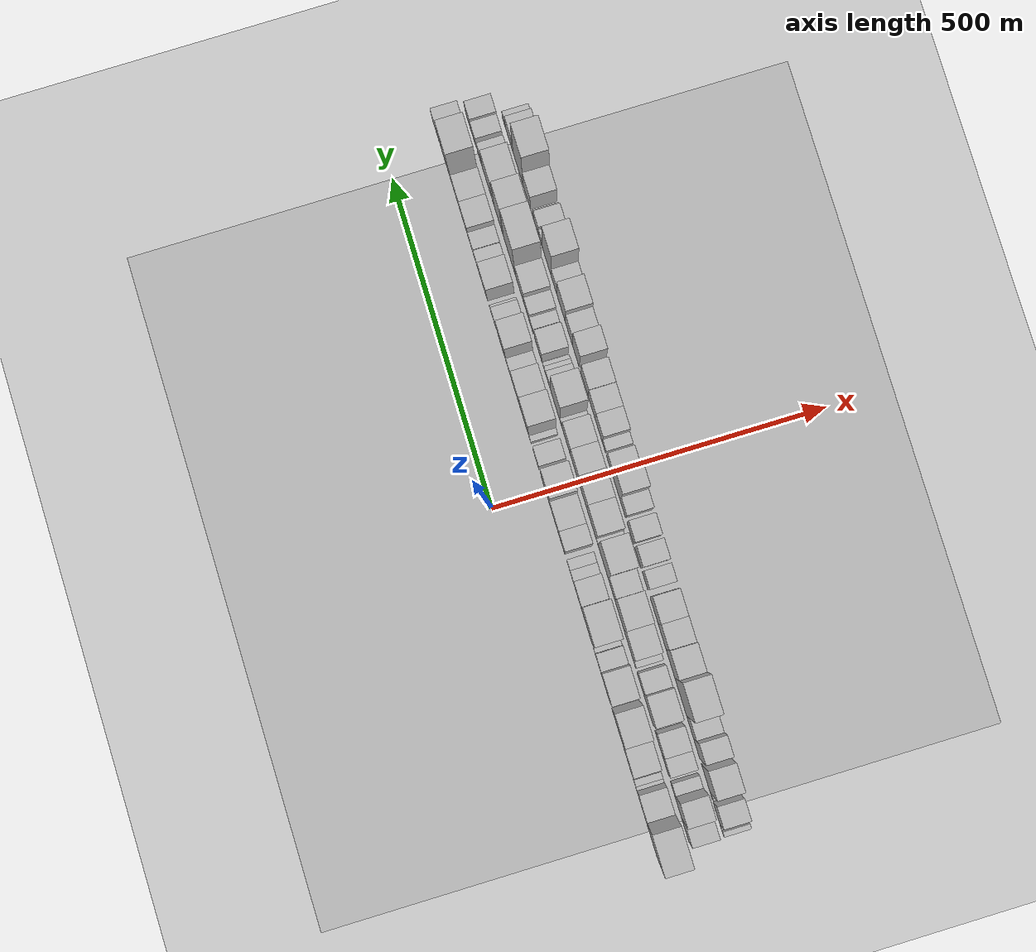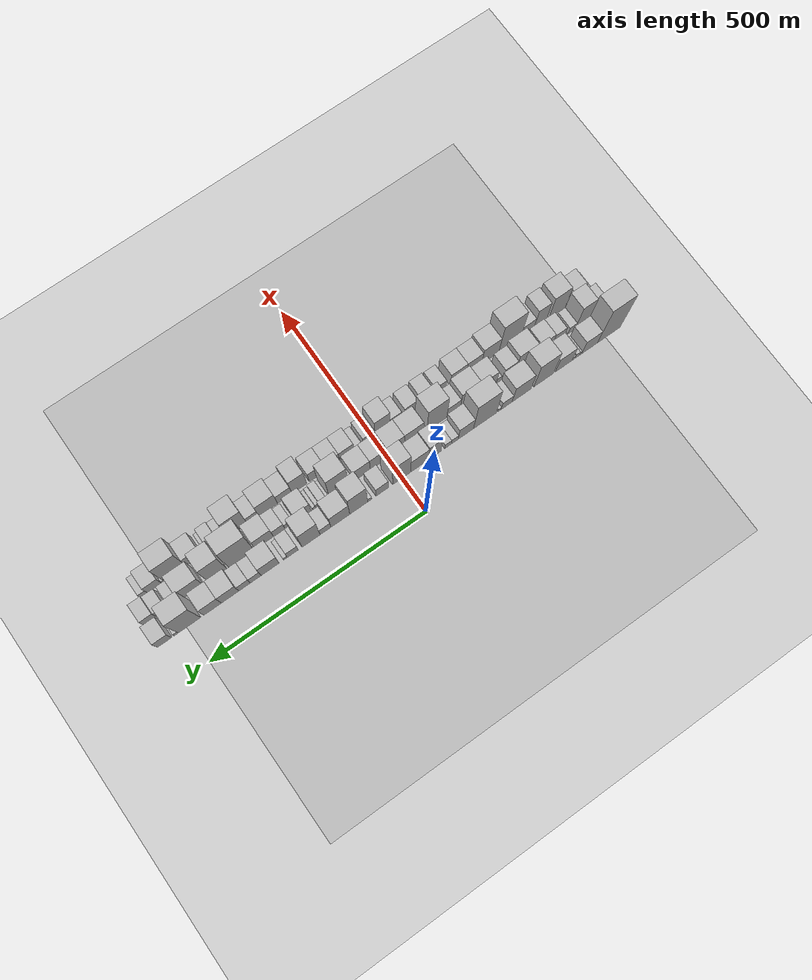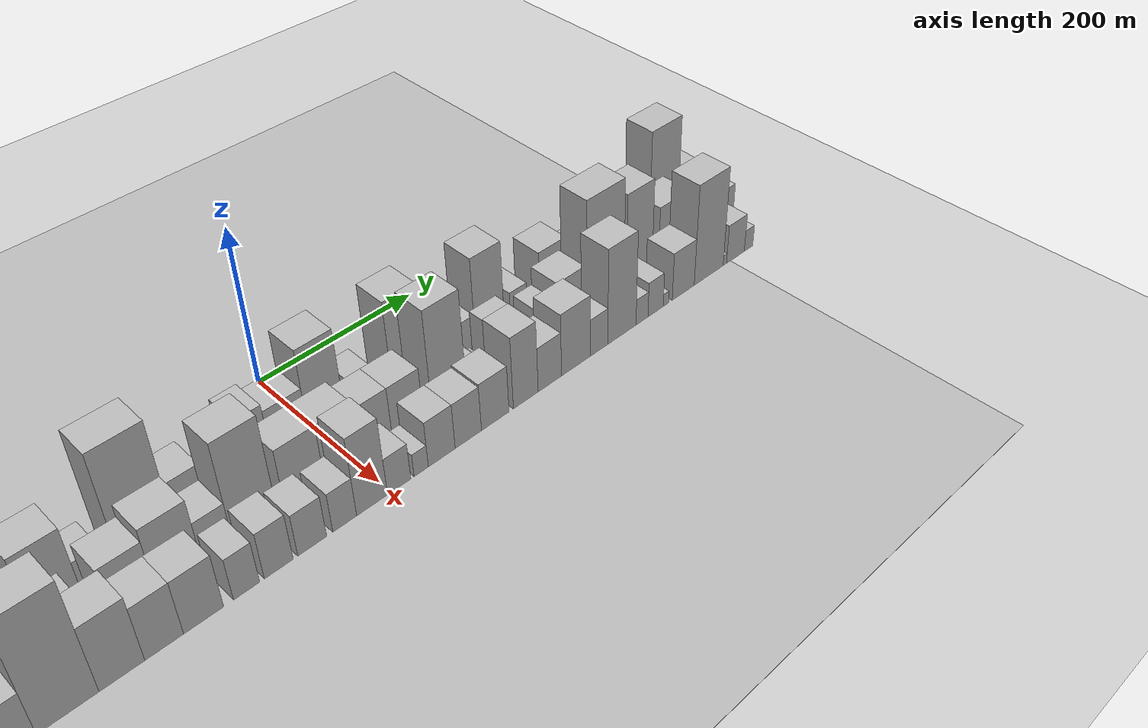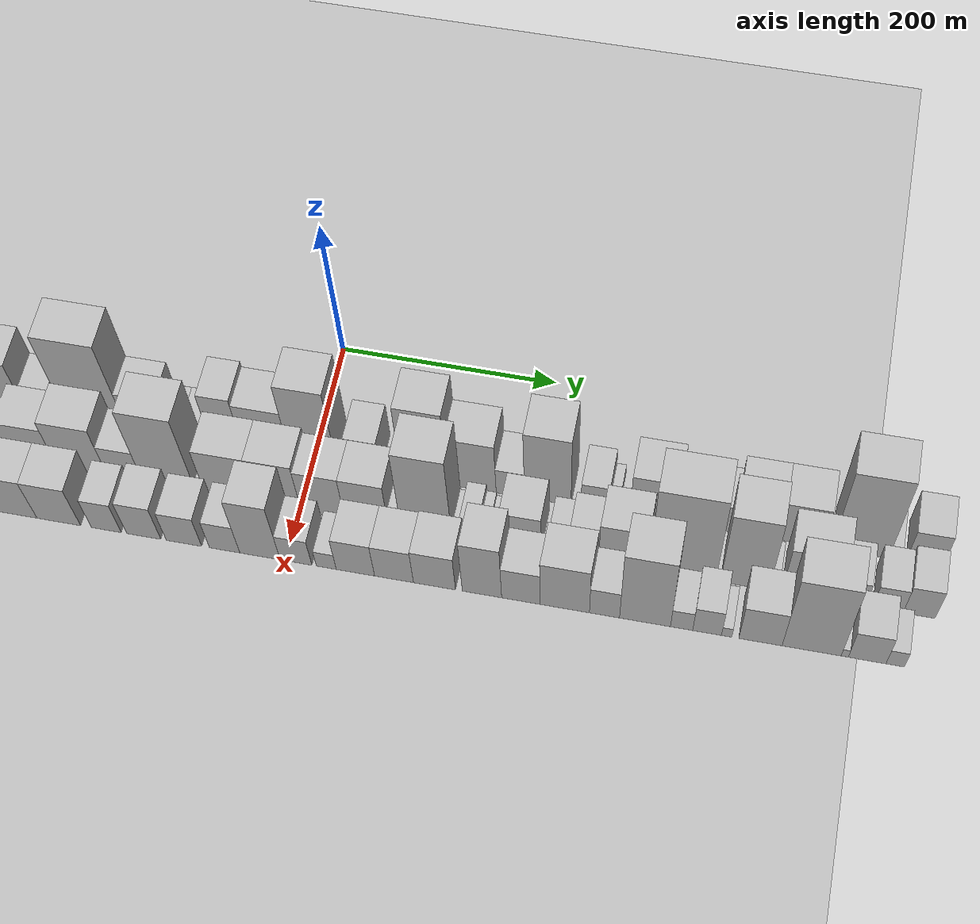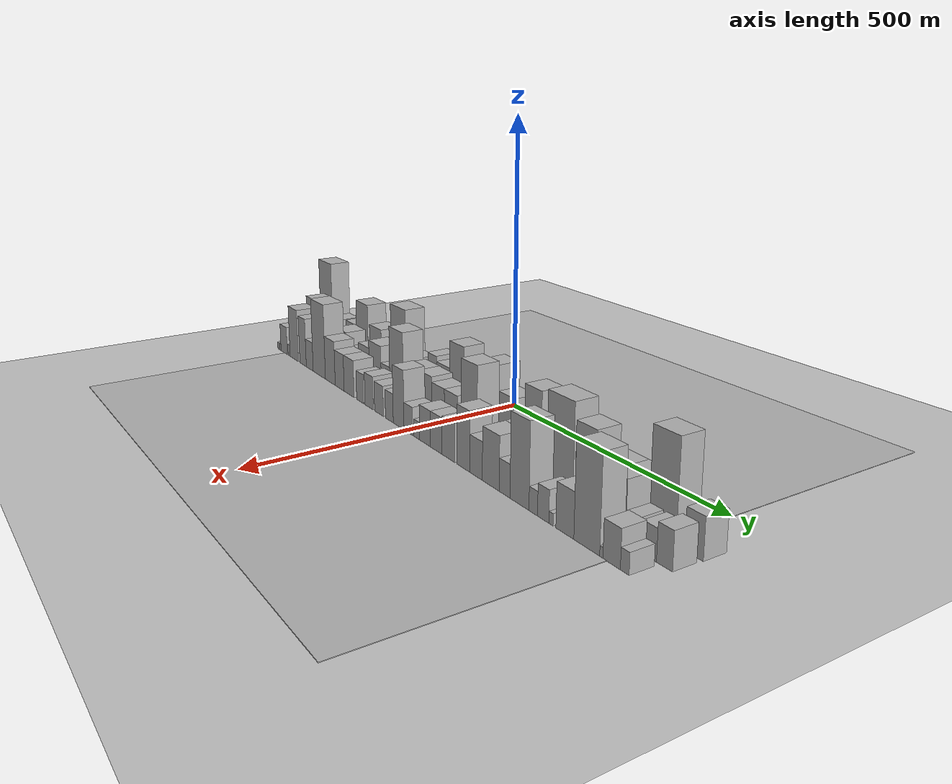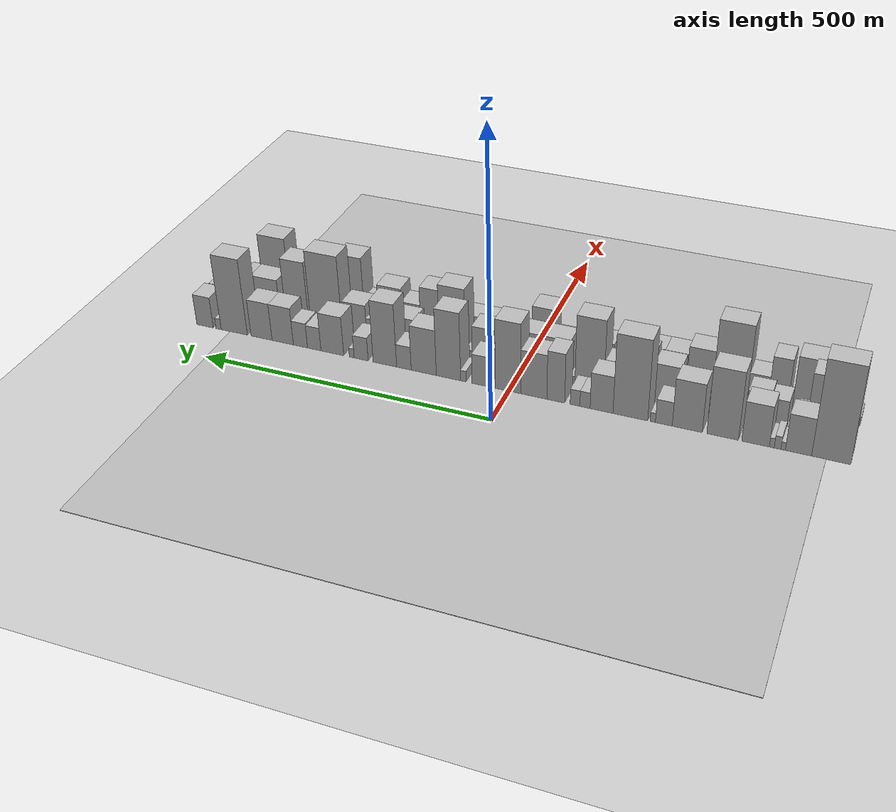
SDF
<?xml version="1.0" encoding="utf-8"?>

<sdf version="1.6">

   <world name="default">

      <gui fullscreen="0">

         <camera name="user_camera">

            <pose>-15 0 4.57585 0 0 0</pose>

            <view_controller>orbit</view_controller>

         </camera>

      </gui>

      <scene>

         <sky>

           <clouds>

             <speed>12</speed>

           </clouds>

         </sky>

         <ambient>0.4 0.4 0.4 1</ambient>

         <background>0.7 0.7 0.7 1</background>

         <shadows>1</shadows>

      </scene>

      <gravity>0 0 -9.8066</gravity>

      <magnetic_field>6e-06 2.3e-05 -4.2e-05</magnetic_field>

      <physics default="0" name="default_physics" type="ode">

         <ode>

            <solver>

               <type>quick</type>

               <iters>10</iters>

               <sor>1.0</sor>

               <use_dynamic_moi_rescaling>0</use_dynamic_moi_rescaling>

            </solver>

            <constraints>

               <cfm>0</cfm>

               <erp>0.2</erp>

               <contact_max_correcting_vel>100</contact_max_correcting_vel>

               <contact_surface_layer>0.001</contact_surface_layer>

            </constraints>

         </ode>

         <max_step_size>0.004</max_step_size>

         <real_time_factor>1</real_time_factor>

         <real_time_update_rate>250</real_time_update_rate>

      </physics>

      <light name="sun" type="directional">

         <cast_shadows>1</cast_shadows>

         <pose>0 0 10 0 0 0</pose>

         <diffuse>0.8 0.8 0.8 1</diffuse>

         <specular>0.2 0.2 0.2 1</specular>

         <attenuation>

            <range>1000</range>

            <constant>0.9</constant>

            <linear>0.01</linear>

            <quadratic>0.001</quadratic>

         </attenuation>

         <direction>-0.5 0.1 -0.9</direction>

      </light>

      <include>

         <name>ground_plane_1</name>

         <uri>model://HANNAS_ground_plane</uri>

         <pose>0 0 0  0 0 0</pose>

      </include>

      <include>

         <name>ground_plane_2</name>

         <uri>model://HANNAS_ground_plane</uri>

         <pose>100 0 0  0 0 0</pose>

      </include>

      <model name="building_1">

         <static>1</static>

         <pose frame="">100.0000 -507.1463 0 0.000000 0.000000 0.000000</pose>

         <link name="link">

            <pose frame="">0 0 88.50 0 0 0</pose>

            <collision name="collision">

               <geometry>

                  <box>

                     <size>40.0000 57.7073 177.0000</size>

                  </box>

               </geometry>

               <max_contacts>10</max_contacts>

               <surface>

                  <contact>

                     <ode/>

                  </contact>

                  <bounce/>

                  <friction>

                     <torsional>

                        <ode/>

                     </torsional>

                     <ode/>

                  </friction>

               </surface>

            </collision>

            <visual name="visual">

               <cast_shadows>0</cast_shadows>

               <geometry>

                  <box>

                     <size>40.0000 57.7073 177.0000</size>

                  </box>

               </geometry>

               <material>

                  <script>

                     <uri>model://HANNAS_wall/materials/scripts</uri>

                     <uri>model://HANNAS_wall/materials/textures</uri>

                     <name>vrc/HANNAS_wall</name>

                  </script>

               </material>

            </visual>

            <self_collide>0</self_collide>

            <enable_wind>0</enable_wind>

            <kinematic>0</kinematic>

         </link>

      </model>

      <model name="building_2">

         <static>1</static>

         <pose frame="">100.0000 -458.8151 0 0.000000 0.000000 0.000000</pose>

         <link name="link">

            <pose frame="">0 0 34.50 0 0 0</pose>

            <collision name="collision">

               <geometry>

                  <box>

                     <size>40.0000 38.9551 69.0000</size>

                  </box>

               </geometry>

               <max_contacts>10</max_contacts>

               <surface>

                  <contact>

                     <ode/>

                  </contact>

                  <bounce/>

                  <friction>

                     <torsional>

                        <ode/>

                     </torsional>

                     <ode/>

                  </friction>

               </surface>

            </collision>

            <visual name="visual">

               <cast_shadows>0</cast_shadows>

               <geometry>

                  <box>

                     <size>40.0000 38.9551 69.0000</size>

                  </box>

               </geometry>

               <material>

                  <script>

                     <uri>model://HANNAS_wall/materials/scripts</uri>

                     <uri>model://HANNAS_wall/materials/textures</uri>

                     <name>vrc/HANNAS_wall</name>

                  </script>

               </material>

            </visual>

            <self_collide>0</self_collide>

            <enable_wind>0</enable_wind>

            <kinematic>0</kinematic>

         </link>

      </model>

      <model name="building_3">

         <static>1</static>

         <pose frame="">100.0000 -436.0091 0 0.000000 0.000000 0.000000</pose>

         <link name="link">

            <pose frame="">0 0 7.50 0 0 0</pose>

            <collision name="collision">

               <geometry>

                  <box>

                     <size>40.0000 6.6569 15.0000</size>

                  </box>

               </geometry>

               <max_contacts>10</max_contacts>

               <surface>

                  <contact>

                     <ode/>

                  </contact>

                  <bounce/>

                  <friction>

                     <torsional>

                        <ode/>

                     </torsional>

                     <ode/>

                  </friction>

               </surface>

            </collision>

            <visual name="visual">

               <cast_shadows>0</cast_shadows>

               <geometry>

                  <box>

                     <size>40.0000 6.6569 15.0000</size>

                  </box>

               </geometry>

               <material>

                  <script>

                     <uri>model://HANNAS_wall/materials/scripts</uri>

                     <uri>model://HANNAS_wall/materials/textures</uri>

                     <name>vrc/HANNAS_wall</name>

                  </script>

               </material>

            </visual>

            <self_collide>0</self_collide>

            <enable_wind>0</enable_wind>

            <kinematic>0</kinematic>

         </link>

      </model>

      <model name="building_4">

         <static>1</static>

         <pose frame="">100.0000 -427.6124 0 0.000000 0.000000 0.000000</pose>

         <link name="link">

            <pose frame="">0 0 12.00 0 0 0</pose>

            <collision name="collision">

               <geometry>

                  <box>

                     <size>40.0000 10.1366 24.0000</size>

                  </box>

               </geometry>

               <max_contacts>10</max_contacts>

               <surface>

                  <contact>

                     <ode/>

                  </contact>

                  <bounce/>

                  <friction>

                     <torsional>

                        <ode/>

                     </torsional>

                     <ode/>

                  </friction>

               </surface>

            </collision>

            <visual name="visual">

               <cast_shadows>0</cast_shadows>

               <geometry>

                  <box>

                     <size>40.0000 10.1366 24.0000</size>

                  </box>

               </geometry>

               <material>

                  <script>

                     <uri>model://HANNAS_wall/materials/scripts</uri>

                     <uri>model://HANNAS_wall/materials/textures</uri>

                     <name>vrc/HANNAS_wall</name>

                  </script>

               </material>

            </visual>

            <self_collide>0</self_collide>

            <enable_wind>0</enable_wind>

            <kinematic>0</kinematic>

         </link>

      </model>

      <model name="building_5">

         <static>1</static>

         <pose frame="">100.0000 -418.8842 0 0.000000 0.000000 0.000000</pose>

         <link name="link">

            <pose frame="">0 0 9.00 0 0 0</pose>

            <collision name="collision">

               <geometry>

                  <box>

                     <size>40.0000 7.3197 18.0000</size>

                  </box>

               </geometry>

               <max_contacts>10</max_contacts>

               <surface>

                  <contact>

                     <ode/>

                  </contact>

                  <bounce/>

                  <friction>

                     <torsional>

                        <ode/>

                     </torsional>

                     <ode/>

                  </friction>

               </surface>

            </collision>

            <visual name="visual">

               <cast_shadows>0</cast_shadows>

               <geometry>

                  <box>

                     <size>40.0000 7.3197 18.0000</size>

                  </box>

               </geometry>

               <material>

                  <script>

                     <uri>model://HANNAS_wall/materials/scripts</uri>

                     <uri>model://HANNAS_wall/materials/textures</uri>

                     <name>vrc/HANNAS_wall</name>

                  </script>

               </material>

            </visual>

            <self_collide>0</self_collide>

            <enable_wind>0</enable_wind>

            <kinematic>0</kinematic>

         </link>

      </model>

      <model name="building_6">

         <static>1</static>

         <pose frame="">100.0000 -394.3049 0 0.000000 0.000000 0.000000</pose>

         <link name="link">

            <pose frame="">0 0 37.50 0 0 0</pose>

            <collision name="collision">

               <geometry>

                  <box>

                     <size>40.0000 41.8389 75.0000</size>

                  </box>

               </geometry>

               <max_contacts>10</max_contacts>

               <surface>

                  <contact>

                     <ode/>

                  </contact>

                  <bounce/>

                  <friction>

                     <torsional>

                        <ode/>

                     </torsional>

                     <ode/>

                  </friction>

               </surface>

            </collision>

            <visual name="visual">

               <cast_shadows>0</cast_shadows>

               <geometry>

                  <box>

                     <size>40.0000 41.8389 75.0000</size>

                  </box>

               </geometry>

               <material>

                  <script>

                     <uri>model://HANNAS_wall/materials/scripts</uri>

                     <uri>model://HANNAS_wall/materials/textures</uri>

                     <name>vrc/HANNAS_wall</name>

                  </script>

               </material>

            </visual>

            <self_collide>0</self_collide>

            <enable_wind>0</enable_wind>

            <kinematic>0</kinematic>

         </link>

      </model>

      <model name="building_7">

         <static>1</static>

         <pose frame="">100.0000 -344.0526 0 0.000000 0.000000 0.000000</pose>

         <link name="link">

            <pose frame="">0 0 63.00 0 0 0</pose>

            <collision name="collision">

               <geometry>

                  <box>

                     <size>40.0000 48.6657 126.0000</size>

                  </box>

               </geometry>

               <max_contacts>10</max_contacts>

               <surface>

                  <contact>

                     <ode/>

                  </contact>

                  <bounce/>

                  <friction>

                     <torsional>

                        <ode/>

                     </torsional>

                     <ode/>

                  </friction>

               </surface>

            </collision>

            <visual name="visual">

               <cast_shadows>0</cast_shadows>

               <geometry>

                  <box>

                     <size>40.0000 48.6657 126.0000</size>

                  </box>

               </geometry>

               <material>

                  <script>

                     <uri>model://HANNAS_wall/materials/scripts</uri>

                     <uri>model://HANNAS_wall/materials/textures</uri>

                     <name>vrc/HANNAS_wall</name>

                  </script>

               </material>

            </visual>

            <self_collide>0</self_collide>

            <enable_wind>0</enable_wind>

            <kinematic>0</kinematic>

         </link>

      </model>

      <model name="building_8">

         <static>1</static>

         <pose frame="">100.0000 -289.3071 0 0.000000 0.000000 0.000000</pose>

         <link name="link">

            <pose frame="">0 0 45.00 0 0 0</pose>

            <collision name="collision">

               <geometry>

                  <box>

                     <size>40.0000 46.8253 90.0000</size>

                  </box>

               </geometry>

               <max_contacts>10</max_contacts>

               <surface>

                  <contact>

                     <ode/>

                  </contact>

                  <bounce/>

                  <friction>

                     <torsional>

                        <ode/>

                     </torsional>

                     <ode/>

                  </friction>

               </surface>

            </collision>

            <visual name="visual">

               <cast_shadows>0</cast_shadows>

               <geometry>

                  <box>

                     <size>40.0000 46.8253 90.0000</size>

                  </box>

               </geometry>

               <material>

                  <script>

                     <uri>model://HANNAS_wall/materials/scripts</uri>

                     <uri>model://HANNAS_wall/materials/textures</uri>

                     <name>vrc/HANNAS_wall</name>

                  </script>

               </material>

            </visual>

            <self_collide>0</self_collide>

            <enable_wind>0</enable_wind>

            <kinematic>0</kinematic>

         </link>

      </model>

      <model name="building_9">

         <static>1</static>

         <pose frame="">100.0000 -252.6126 0 0.000000 0.000000 0.000000</pose>

         <link name="link">

            <pose frame="">0 0 22.50 0 0 0</pose>

            <collision name="collision">

               <geometry>

                  <box>

                     <size>40.0000 26.5637 45.0000</size>

                  </box>

               </geometry>

               <max_contacts>10</max_contacts>

               <surface>

                  <contact>

                     <ode/>

                  </contact>

                  <bounce/>

                  <friction>

                     <torsional>

                        <ode/>

                     </torsional>

                     <ode/>

                  </friction>

               </surface>

            </collision>

            <visual name="visual">

               <cast_shadows>0</cast_shadows>

               <geometry>

                  <box>

                     <size>40.0000 26.5637 45.0000</size>

                  </box>

               </geometry>

               <material>

                  <script>

                     <uri>model://HANNAS_wall/materials/scripts</uri>

                     <uri>model://HANNAS_wall/materials/textures</uri>

                     <name>vrc/HANNAS_wall</name>

                  </script>

               </material>

            </visual>

            <self_collide>0</self_collide>

            <enable_wind>0</enable_wind>

            <kinematic>0</kinematic>

         </link>

      </model>

      <model name="building_10">

         <static>1</static>

         <pose frame="">100.0000 -235.2382 0 0.000000 0.000000 0.000000</pose>

         <link name="link">

            <pose frame="">0 0 9.00 0 0 0</pose>

            <collision name="collision">

               <geometry>

                  <box>

                     <size>40.0000 8.1850 18.0000</size>

                  </box>

               </geometry>

               <max_contacts>10</max_contacts>

               <surface>

                  <contact>

                     <ode/>

                  </contact>

                  <bounce/>

                  <friction>

                     <torsional>

                        <ode/>

                     </torsional>

                     <ode/>

                  </friction>

               </surface>

            </collision>

            <visual name="visual">

               <cast_shadows>0</cast_shadows>

               <geometry>

                  <box>

                     <size>40.0000 8.1850 18.0000</size>

                  </box>

               </geometry>

               <material>

                  <script>

                     <uri>model://HANNAS_wall/materials/scripts</uri>

                     <uri>model://HANNAS_wall/materials/textures</uri>

                     <name>vrc/HANNAS_wall</name>

                  </script>

               </material>

            </visual>

            <self_collide>0</self_collide>

            <enable_wind>0</enable_wind>

            <kinematic>0</kinematic>

         </link>

      </model>

      <model name="building_11">

         <static>1</static>

         <pose frame="">100.0000 -199.3745 0 0.000000 0.000000 0.000000</pose>

         <link name="link">

            <pose frame="">0 0 75.00 0 0 0</pose>

            <collision name="collision">

               <geometry>

                  <box>

                     <size>40.0000 55.5425 150.0000</size>

                  </box>

               </geometry>

               <max_contacts>10</max_contacts>

               <surface>

                  <contact>

                     <ode/>

                  </contact>

                  <bounce/>

                  <friction>

                     <torsional>

                        <ode/>

                     </torsional>

                     <ode/>

                  </friction>

               </surface>

            </collision>

            <visual name="visual">

               <cast_shadows>0</cast_shadows>

               <geometry>

                  <box>

                     <size>40.0000 55.5425 150.0000</size>

                  </box>

               </geometry>

               <material>

                  <script>

                     <uri>model://HANNAS_wall/materials/scripts</uri>

                     <uri>model://HANNAS_wall/materials/textures</uri>

                     <name>vrc/HANNAS_wall</name>

                  </script>

               </material>

            </visual>

            <self_collide>0</self_collide>

            <enable_wind>0</enable_wind>

            <kinematic>0</kinematic>

         </link>

      </model>

      <model name="building_12">

         <static>1</static>

         <pose frame="">100.0000 -153.1089 0 0.000000 0.000000 0.000000</pose>

         <link name="link">

            <pose frame="">0 0 34.50 0 0 0</pose>

            <collision name="collision">

               <geometry>

                  <box>

                     <size>40.0000 36.9888 69.0000</size>

                  </box>

               </geometry>

               <max_contacts>10</max_contacts>

               <surface>

                  <contact>

                     <ode/>

                  </contact>

                  <bounce/>

                  <friction>

                     <torsional>

                        <ode/>

                     </torsional>

                     <ode/>

                  </friction>

               </surface>

            </collision>

            <visual name="visual">

               <cast_shadows>0</cast_shadows>

               <geometry>

                  <box>

                     <size>40.0000 36.9888 69.0000</size>

                  </box>

               </geometry>

               <material>

                  <script>

                     <uri>model://HANNAS_wall/materials/scripts</uri>

                     <uri>model://HANNAS_wall/materials/textures</uri>

                     <name>vrc/HANNAS_wall</name>

                  </script>

               </material>

            </visual>

            <self_collide>0</self_collide>

            <enable_wind>0</enable_wind>

            <kinematic>0</kinematic>

         </link>

      </model>

      <model name="building_13">

         <static>1</static>

         <pose frame="">100.0000 -126.3114 0 0.000000 0.000000 0.000000</pose>

         <link name="link">

            <pose frame="">0 0 15.00 0 0 0</pose>

            <collision name="collision">

               <geometry>

                  <box>

                     <size>40.0000 16.6062 30.0000</size>

                  </box>

               </geometry>

               <max_contacts>10</max_contacts>

               <surface>

                  <contact>

                     <ode/>

                  </contact>

                  <bounce/>

                  <friction>

                     <torsional>

                        <ode/>

                     </torsional>

                     <ode/>

                  </friction>

               </surface>

            </collision>

            <visual name="visual">

               <cast_shadows>0</cast_shadows>

               <geometry>

                  <box>

                     <size>40.0000 16.6062 30.0000</size>

                  </box>

               </geometry>

               <material>

                  <script>

                     <uri>model://HANNAS_wall/materials/scripts</uri>

                     <uri>model://HANNAS_wall/materials/textures</uri>

                     <name>vrc/HANNAS_wall</name>

                  </script>

               </material>

            </visual>

            <self_collide>0</self_collide>

            <enable_wind>0</enable_wind>

            <kinematic>0</kinematic>

         </link>

      </model>

      <model name="building_14">

         <static>1</static>

         <pose frame="">100.0000 -110.0389 0 0.000000 0.000000 0.000000</pose>

         <link name="link">

            <pose frame="">0 0 15.00 0 0 0</pose>

            <collision name="collision">

               <geometry>

                  <box>

                     <size>40.0000 15.9388 30.0000</size>

                  </box>

               </geometry>

               <max_contacts>10</max_contacts>

               <surface>

                  <contact>

                     <ode/>

                  </contact>

                  <bounce/>

                  <friction>

                     <torsional>

                        <ode/>

                     </torsional>

                     <ode/>

                  </friction>

               </surface>

            </collision>

            <visual name="visual">

               <cast_shadows>0</cast_shadows>

               <geometry>

                  <box>

                     <size>40.0000 15.9388 30.0000</size>

                  </box>

               </geometry>

               <material>

                  <script>

                     <uri>model://HANNAS_wall/materials/scripts</uri>

                     <uri>model://HANNAS_wall/materials/textures</uri>

                     <name>vrc/HANNAS_wall</name>

                  </script>

               </material>

            </visual>

            <self_collide>0</self_collide>

            <enable_wind>0</enable_wind>

            <kinematic>0</kinematic>

         </link>

      </model>

      <model name="building_15">

         <static>1</static>

         <pose frame="">100.0000 -78.3775 0 0.000000 0.000000 0.000000</pose>

         <link name="link">

            <pose frame="">0 0 46.50 0 0 0</pose>

            <collision name="collision">

               <geometry>

                  <box>

                     <size>40.0000 29.3840 93.0000</size>

                  </box>

               </geometry>

               <max_contacts>10</max_contacts>

               <surface>

                  <contact>

                     <ode/>

                  </contact>

                  <bounce/>

                  <friction>

                     <torsional>

                        <ode/>

                     </torsional>

                     <ode/>

                  </friction>

               </surface>

            </collision>

            <visual name="visual">

               <cast_shadows>0</cast_shadows>

               <geometry>

                  <box>

                     <size>40.0000 29.3840 93.0000</size>

                  </box>

               </geometry>

               <material>

                  <script>

                     <uri>model://HANNAS_wall/materials/scripts</uri>

                     <uri>model://HANNAS_wall/materials/textures</uri>

                     <name>vrc/HANNAS_wall</name>

                  </script>

               </material>

            </visual>

            <self_collide>0</self_collide>

            <enable_wind>0</enable_wind>

            <kinematic>0</kinematic>

         </link>

      </model>

      <model name="building_16">

         <static>1</static>

         <pose frame="">100.0000 -41.8981 0 0.000000 0.000000 0.000000</pose>

         <link name="link">

            <pose frame="">0 0 42.00 0 0 0</pose>

            <collision name="collision">

               <geometry>

                  <box>

                     <size>40.0000 43.5748 84.0000</size>

                  </box>

               </geometry>

               <max_contacts>10</max_contacts>

               <surface>

                  <contact>

                     <ode/>

                  </contact>

                  <bounce/>

                  <friction>

                     <torsional>

                        <ode/>

                     </torsional>

                     <ode/>

                  </friction>

               </surface>

            </collision>

            <visual name="visual">

               <cast_shadows>0</cast_shadows>

               <geometry>

                  <box>

                     <size>40.0000 43.5748 84.0000</size>

                  </box>

               </geometry>

               <material>

                  <script>

                     <uri>model://HANNAS_wall/materials/scripts</uri>

                     <uri>model://HANNAS_wall/materials/textures</uri>

                     <name>vrc/HANNAS_wall</name>

                  </script>

               </material>

            </visual>

            <self_collide>0</self_collide>

            <enable_wind>0</enable_wind>

            <kinematic>0</kinematic>

         </link>

      </model>

      <model name="building_17">

         <static>1</static>

         <pose frame="">100.0000 1.3072 0 0.000000 0.000000 0.000000</pose>

         <link name="link">

            <pose frame="">0 0 66.00 0 0 0</pose>

            <collision name="collision">

               <geometry>

                  <box>

                     <size>40.0000 42.8359 132.0000</size>

                  </box>

               </geometry>

               <max_contacts>10</max_contacts>

               <surface>

                  <contact>

                     <ode/>

                  </contact>

                  <bounce/>

                  <friction>

                     <torsional>

                        <ode/>

                     </torsional>

                     <ode/>

                  </friction>

               </surface>

            </collision>

            <visual name="visual">

               <cast_shadows>0</cast_shadows>

               <geometry>

                  <box>

                     <size>40.0000 42.8359 132.0000</size>

                  </box>

               </geometry>

               <material>

                  <script>

                     <uri>model://HANNAS_wall/materials/scripts</uri>

                     <uri>model://HANNAS_wall/materials/textures</uri>

                     <name>vrc/HANNAS_wall</name>

                  </script>

               </material>

            </visual>

            <self_collide>0</self_collide>

            <enable_wind>0</enable_wind>

            <kinematic>0</kinematic>

         </link>

      </model>

      <model name="building_18">

         <static>1</static>

         <pose frame="">100.0000 47.5142 0 0.000000 0.000000 0.000000</pose>

         <link name="link">

            <pose frame="">0 0 28.50 0 0 0</pose>

            <collision name="collision">

               <geometry>

                  <box>

                     <size>40.0000 29.5781 57.0000</size>

                  </box>

               </geometry>

               <max_contacts>10</max_contacts>

               <surface>

                  <contact>

                     <ode/>

                  </contact>

                  <bounce/>

                  <friction>

                     <torsional>

                        <ode/>

                     </torsional>

                     <ode/>

                  </friction>

               </surface>

            </collision>

            <visual name="visual">

               <cast_shadows>0</cast_shadows>

               <geometry>

                  <box>

                     <size>40.0000 29.5781 57.0000</size>

                  </box>

               </geometry>

               <material>

                  <script>

                     <uri>model://HANNAS_wall/materials/scripts</uri>

                     <uri>model://HANNAS_wall/materials/textures</uri>

                     <name>vrc/HANNAS_wall</name>

                  </script>

               </material>

            </visual>

            <self_collide>0</self_collide>

            <enable_wind>0</enable_wind>

            <kinematic>0</kinematic>

         </link>

      </model>

      <model name="building_19">

         <static>1</static>

         <pose frame="">100.0000 77.1149 0 0.000000 0.000000 0.000000</pose>

         <link name="link">

            <pose frame="">0 0 10.50 0 0 0</pose>

            <collision name="collision">

               <geometry>

                  <box>

                     <size>40.0000 9.6232 21.0000</size>

                  </box>

               </geometry>

               <max_contacts>10</max_contacts>

               <surface>

                  <contact>

                     <ode/>

                  </contact>

                  <bounce/>

                  <friction>

                     <torsional>

                        <ode/>

                     </torsional>

                     <ode/>

                  </friction>

               </surface>

            </collision>

            <visual name="visual">

               <cast_shadows>0</cast_shadows>

               <geometry>

                  <box>

                     <size>40.0000 9.6232 21.0000</size>

                  </box>

               </geometry>

               <material>

                  <script>

                     <uri>model://HANNAS_wall/materials/scripts</uri>

                     <uri>model://HANNAS_wall/materials/textures</uri>

                     <name>vrc/HANNAS_wall</name>

                  </script>

               </material>

            </visual>

            <self_collide>0</self_collide>

            <enable_wind>0</enable_wind>

            <kinematic>0</kinematic>

         </link>

      </model>

      <model name="building_20">

         <static>1</static>

         <pose frame="">100.0000 103.0087 0 0.000000 0.000000 0.000000</pose>

         <link name="link">

            <pose frame="">0 0 64.50 0 0 0</pose>

            <collision name="collision">

               <geometry>

                  <box>

                     <size>40.0000 42.1644 129.0000</size>

                  </box>

               </geometry>

               <max_contacts>10</max_contacts>

               <surface>

                  <contact>

                     <ode/>

                  </contact>

                  <bounce/>

                  <friction>

                     <torsional>

                        <ode/>

                     </torsional>

                     <ode/>

                  </friction>

               </surface>

            </collision>

            <visual name="visual">

               <cast_shadows>0</cast_shadows>

               <geometry>

                  <box>

                     <size>40.0000 42.1644 129.0000</size>

                  </box>

               </geometry>

               <material>

                  <script>

                     <uri>model://HANNAS_wall/materials/scripts</uri>

                     <uri>model://HANNAS_wall/materials/textures</uri>

                     <name>vrc/HANNAS_wall</name>

                  </script>

               </material>

            </visual>

            <self_collide>0</self_collide>

            <enable_wind>0</enable_wind>

            <kinematic>0</kinematic>

         </link>

      </model>

      <model name="building_21">

         <static>1</static>

         <pose frame="">100.0000 146.0531 0 0.000000 0.000000 0.000000</pose>

         <link name="link">

            <pose frame="">0 0 43.50 0 0 0</pose>

            <collision name="collision">

               <geometry>

                  <box>

                     <size>40.0000 43.9245 87.0000</size>

                  </box>

               </geometry>

               <max_contacts>10</max_contacts>

               <surface>

                  <contact>

                     <ode/>

                  </contact>

                  <bounce/>

                  <friction>

                     <torsional>

                        <ode/>

                     </torsional>

                     <ode/>

                  </friction>

               </surface>

            </collision>

            <visual name="visual">

               <cast_shadows>0</cast_shadows>

               <geometry>

                  <box>

                     <size>40.0000 43.9245 87.0000</size>

                  </box>

               </geometry>

               <material>

                  <script>

                     <uri>model://HANNAS_wall/materials/scripts</uri>

                     <uri>model://HANNAS_wall/materials/textures</uri>

                     <name>vrc/HANNAS_wall</name>

                  </script>

               </material>

            </visual>

            <self_collide>0</self_collide>

            <enable_wind>0</enable_wind>

            <kinematic>0</kinematic>

         </link>

      </model>

      <model name="building_22">

         <static>1</static>

         <pose frame="">100.0000 180.8599 0 0.000000 0.000000 0.000000</pose>

         <link name="link">

            <pose frame="">0 0 22.50 0 0 0</pose>

            <collision name="collision">

               <geometry>

                  <box>

                     <size>40.0000 25.6891 45.0000</size>

                  </box>

               </geometry>

               <max_contacts>10</max_contacts>

               <surface>

                  <contact>

                     <ode/>

                  </contact>

                  <bounce/>

                  <friction>

                     <torsional>

                        <ode/>

                     </torsional>

                     <ode/>

                  </friction>

               </surface>

            </collision>

            <visual name="visual">

               <cast_shadows>0</cast_shadows>

               <geometry>

                  <box>

                     <size>40.0000 25.6891 45.0000</size>

                  </box>

               </geometry>

               <material>

                  <script>

                     <uri>model://HANNAS_wall/materials/scripts</uri>

                     <uri>model://HANNAS_wall/materials/textures</uri>

                     <name>vrc/HANNAS_wall</name>

                  </script>

               </material>

            </visual>

            <self_collide>0</self_collide>

            <enable_wind>0</enable_wind>

            <kinematic>0</kinematic>

         </link>

      </model>

      <model name="building_23">

         <static>1</static>

         <pose frame="">100.0000 214.6392 0 0.000000 0.000000 0.000000</pose>

         <link name="link">

            <pose frame="">0 0 60.00 0 0 0</pose>

            <collision name="collision">

               <geometry>

                  <box>

                     <size>40.0000 41.8695 120.0000</size>

                  </box>

               </geometry>

               <max_contacts>10</max_contacts>

               <surface>

                  <contact>

                     <ode/>

                  </contact>

                  <bounce/>

                  <friction>

                     <torsional>

                        <ode/>

                     </torsional>

                     <ode/>

                  </friction>

               </surface>

            </collision>

            <visual name="visual">

               <cast_shadows>0</cast_shadows>

               <geometry>

                  <box>

                     <size>40.0000 41.8695 120.0000</size>

                  </box>

               </geometry>

               <material>

                  <script>

                     <uri>model://HANNAS_wall/materials/scripts</uri>

                     <uri>model://HANNAS_wall/materials/textures</uri>

                     <name>vrc/HANNAS_wall</name>

                  </script>

               </material>

            </visual>

            <self_collide>0</self_collide>

            <enable_wind>0</enable_wind>

            <kinematic>0</kinematic>

         </link>

      </model>

      <model name="building_24">

         <static>1</static>

         <pose frame="">100.0000 257.1853 0 0.000000 0.000000 0.000000</pose>

         <link name="link">

            <pose frame="">0 0 22.50 0 0 0</pose>

            <collision name="collision">

               <geometry>

                  <box>

                     <size>40.0000 25.2226 45.0000</size>

                  </box>

               </geometry>

               <max_contacts>10</max_contacts>

               <surface>

                  <contact>

                     <ode/>

                  </contact>

                  <bounce/>

                  <friction>

                     <torsional>

                        <ode/>

                     </torsional>

                     <ode/>

                  </friction>

               </surface>

            </collision>

            <visual name="visual">

               <cast_shadows>0</cast_shadows>

               <geometry>

                  <box>

                     <size>40.0000 25.2226 45.0000</size>

                  </box>

               </geometry>

               <material>

                  <script>

                     <uri>model://HANNAS_wall/materials/scripts</uri>

                     <uri>model://HANNAS_wall/materials/textures</uri>

                     <name>vrc/HANNAS_wall</name>

                  </script>

               </material>

            </visual>

            <self_collide>0</self_collide>

            <enable_wind>0</enable_wind>

            <kinematic>0</kinematic>

         </link>

      </model>

      <model name="building_25">

         <static>1</static>

         <pose frame="">100.0000 274.1610 0 0.000000 0.000000 0.000000</pose>

         <link name="link">

            <pose frame="">0 0 9.00 0 0 0</pose>

            <collision name="collision">

               <geometry>

                  <box>

                     <size>40.0000 8.7289 18.0000</size>

                  </box>

               </geometry>

               <max_contacts>10</max_contacts>

               <surface>

                  <contact>

                     <ode/>

                  </contact>

                  <bounce/>

                  <friction>

                     <torsional>

                        <ode/>

                     </torsional>

                     <ode/>

                  </friction>

               </surface>

            </collision>

            <visual name="visual">

               <cast_shadows>0</cast_shadows>

               <geometry>

                  <box>

                     <size>40.0000 8.7289 18.0000</size>

                  </box>

               </geometry>

               <material>

                  <script>

                     <uri>model://HANNAS_wall/materials/scripts</uri>

                     <uri>model://HANNAS_wall/materials/textures</uri>

                     <name>vrc/HANNAS_wall</name>

                  </script>

               </material>

            </visual>

            <self_collide>0</self_collide>

            <enable_wind>0</enable_wind>

            <kinematic>0</kinematic>

         </link>

      </model>

      <model name="building_26">

         <static>1</static>

         <pose frame="">100.0000 309.3299 0 0.000000 0.000000 0.000000</pose>

         <link name="link">

            <pose frame="">0 0 37.50 0 0 0</pose>

            <collision name="collision">

               <geometry>

                  <box>

                     <size>40.0000 41.6088 75.0000</size>

                  </box>

               </geometry>

               <max_contacts>10</max_contacts>

               <surface>

                  <contact>

                     <ode/>

                  </contact>

                  <bounce/>

                  <friction>

                     <torsional>

                        <ode/>

                     </torsional>

                     <ode/>

                  </friction>

               </surface>

            </collision>

            <visual name="visual">

               <cast_shadows>0</cast_shadows>

               <geometry>

                  <box>

                     <size>40.0000 41.6088 75.0000</size>

                  </box>

               </geometry>

               <material>

                  <script>

                     <uri>model://HANNAS_wall/materials/scripts</uri>

                     <uri>model://HANNAS_wall/materials/textures</uri>

                     <name>vrc/HANNAS_wall</name>

                  </script>

               </material>

            </visual>

            <self_collide>0</self_collide>

            <enable_wind>0</enable_wind>

            <kinematic>0</kinematic>

         </link>

      </model>

      <model name="building_27">

         <static>1</static>

         <pose frame="">100.0000 342.5197 0 0.000000 0.000000 0.000000</pose>

         <link name="link">

            <pose frame="">0 0 22.50 0 0 0</pose>

            <collision name="collision">

               <geometry>

                  <box>

                     <size>40.0000 24.7709 45.0000</size>

                  </box>

               </geometry>

               <max_contacts>10</max_contacts>

               <surface>

                  <contact>

                     <ode/>

                  </contact>

                  <bounce/>

                  <friction>

                     <torsional>

                        <ode/>

                     </torsional>

                     <ode/>

                  </friction>

               </surface>

            </collision>

            <visual name="visual">

               <cast_shadows>0</cast_shadows>

               <geometry>

                  <box>

                     <size>40.0000 24.7709 45.0000</size>

                  </box>

               </geometry>

               <material>

                  <script>

                     <uri>model://HANNAS_wall/materials/scripts</uri>

                     <uri>model://HANNAS_wall/materials/textures</uri>

                     <name>vrc/HANNAS_wall</name>

                  </script>

               </material>

            </visual>

            <self_collide>0</self_collide>

            <enable_wind>0</enable_wind>

            <kinematic>0</kinematic>

         </link>

      </model>

      <model name="building_28">

         <static>1</static>

         <pose frame="">100.0000 368.0168 0 0.000000 0.000000 0.000000</pose>

         <link name="link">

            <pose frame="">0 0 24.00 0 0 0</pose>

            <collision name="collision">

               <geometry>

                  <box>

                     <size>40.0000 26.2232 48.0000</size>

                  </box>

               </geometry>

               <max_contacts>10</max_contacts>

               <surface>

                  <contact>

                     <ode/>

                  </contact>

                  <bounce/>

                  <friction>

                     <torsional>

                        <ode/>

                     </torsional>

                     <ode/>

                  </friction>

               </surface>

            </collision>

            <visual name="visual">

               <cast_shadows>0</cast_shadows>

               <geometry>

                  <box>

                     <size>40.0000 26.2232 48.0000</size>

                  </box>

               </geometry>

               <material>

                  <script>

                     <uri>model://HANNAS_wall/materials/scripts</uri>

                     <uri>model://HANNAS_wall/materials/textures</uri>

                     <name>vrc/HANNAS_wall</name>

                  </script>

               </material>

            </visual>

            <self_collide>0</self_collide>

            <enable_wind>0</enable_wind>

            <kinematic>0</kinematic>

         </link>

      </model>

      <model name="building_29">

         <static>1</static>

         <pose frame="">100.0000 400.9794 0 0.000000 0.000000 0.000000</pose>

         <link name="link">

            <pose frame="">0 0 36.00 0 0 0</pose>

            <collision name="collision">

               <geometry>

                  <box>

                     <size>40.0000 39.7020 72.0000</size>

                  </box>

               </geometry>

               <max_contacts>10</max_contacts>

               <surface>

                  <contact>

                     <ode/>

                  </contact>

                  <bounce/>

                  <friction>

                     <torsional>

                        <ode/>

                     </torsional>

                     <ode/>

                  </friction>

               </surface>

            </collision>

            <visual name="visual">

               <cast_shadows>0</cast_shadows>

               <geometry>

                  <box>

                     <size>40.0000 39.7020 72.0000</size>

                  </box>

               </geometry>

               <material>

                  <script>

                     <uri>model://HANNAS_wall/materials/scripts</uri>

                     <uri>model://HANNAS_wall/materials/textures</uri>

                     <name>vrc/HANNAS_wall</name>

                  </script>

               </material>

            </visual>

            <self_collide>0</self_collide>

            <enable_wind>0</enable_wind>

            <kinematic>0</kinematic>

         </link>

      </model>

      <model name="building_30">

         <static>1</static>

         <pose frame="">100.0000 440.6748 0 0.000000 0.000000 0.000000</pose>

         <link name="link">

            <pose frame="">0 0 36.00 0 0 0</pose>

            <collision name="collision">

               <geometry>

                  <box>

                     <size>40.0000 39.6888 72.0000</size>

                  </box>

               </geometry>

               <max_contacts>10</max_contacts>

               <surface>

                  <contact>

                     <ode/>

                  </contact>

                  <bounce/>

                  <friction>

                     <torsional>

                        <ode/>

                     </torsional>

                     <ode/>

                  </friction>

               </surface>

            </collision>

            <visual name="visual">

               <cast_shadows>0</cast_shadows>

               <geometry>

                  <box>

                     <size>40.0000 39.6888 72.0000</size>

                  </box>

               </geometry>

               <material>

                  <script>

                     <uri>model://HANNAS_wall/materials/scripts</uri>

                     <uri>model://HANNAS_wall/materials/textures</uri>

                     <name>vrc/HANNAS_wall</name>

                  </script>

               </material>

            </visual>

            <self_collide>0</self_collide>

            <enable_wind>0</enable_wind>

            <kinematic>0</kinematic>

         </link>

      </model>

      <model name="building_31">

         <static>1</static>

         <pose frame="">100.0000 492.5339 0 0.000000 0.000000 0.000000</pose>

         <link name="link">

            <pose frame="">0 0 73.50 0 0 0</pose>

            <collision name="collision">

               <geometry>

                  <box>

                     <size>40.0000 50.0295 147.0000</size>

                  </box>

               </geometry>

               <max_contacts>10</max_contacts>

               <surface>

                  <contact>

                     <ode/>

                  </contact>

                  <bounce/>

                  <friction>

                     <torsional>

                        <ode/>

                     </torsional>

                     <ode/>

                  </friction>

               </surface>

            </collision>

            <visual name="visual">

               <cast_shadows>0</cast_shadows>

               <geometry>

                  <box>

                     <size>40.0000 50.0295 147.0000</size>

                  </box>

               </geometry>

               <material>

                  <script>

                     <uri>model://HANNAS_wall/materials/scripts</uri>

                     <uri>model://HANNAS_wall/materials/textures</uri>

                     <name>vrc/HANNAS_wall</name>

                  </script>

               </material>

            </visual>

            <self_collide>0</self_collide>

            <enable_wind>0</enable_wind>

            <kinematic>0</kinematic>

         </link>

      </model>

      <model name="building_32">

         <static>1</static>

         <pose frame="">100.0000 522.5782 0 0.000000 0.000000 0.000000</pose>

         <link name="link">

            <pose frame="">0 0 10.50 0 0 0</pose>

            <collision name="collision">

               <geometry>

                  <box>

                     <size>40.0000 10.0590 21.0000</size>

                  </box>

               </geometry>

               <max_contacts>10</max_contacts>

               <surface>

                  <contact>

                     <ode/>

                  </contact>

                  <bounce/>

                  <friction>

                     <torsional>

                        <ode/>

                     </torsional>

                     <ode/>

                  </friction>

               </surface>

            </collision>

            <visual name="visual">

               <cast_shadows>0</cast_shadows>

               <geometry>

                  <box>

                     <size>40.0000 10.0590 21.0000</size>

                  </box>

               </geometry>

               <material>

                  <script>

                     <uri>model://HANNAS_wall/materials/scripts</uri>

                     <uri>model://HANNAS_wall/materials/textures</uri>

                     <name>vrc/HANNAS_wall</name>

                  </script>

               </material>

            </visual>

            <self_collide>0</self_collide>

            <enable_wind>0</enable_wind>

            <kinematic>0</kinematic>

         </link>

      </model>

      <model name="building_33">

         <static>1</static>

         <pose frame="">100.0000 548.5103 0 0.000000 0.000000 0.000000</pose>

         <link name="link">

            <pose frame="">0 0 30.00 0 0 0</pose>

            <collision name="collision">

               <geometry>

                  <box>

                     <size>40.0000 31.8052 60.0000</size>

                  </box>

               </geometry>

               <max_contacts>10</max_contacts>

               <surface>

                  <contact>

                     <ode/>

                  </contact>

                  <bounce/>

                  <friction>

                     <torsional>

                        <ode/>

                     </torsional>

                     <ode/>

                  </friction>

               </surface>

            </collision>

            <visual name="visual">

               <cast_shadows>0</cast_shadows>

               <geometry>

                  <box>

                     <size>40.0000 31.8052 60.0000</size>

                  </box>

               </geometry>

               <material>

                  <script>

                     <uri>model://HANNAS_wall/materials/scripts</uri>

                     <uri>model://HANNAS_wall/materials/textures</uri>

                     <name>vrc/HANNAS_wall</name>

                  </script>

               </material>

            </visual>

            <self_collide>0</self_collide>

            <enable_wind>0</enable_wind>

            <kinematic>0</kinematic>

         </link>

      </model>

      <model name="building_34">

         <static>1</static>

         <pose frame="">149.0000 -512.0052 0 0.000000 0.000000 0.000000</pose>

         <link name="link">

            <pose frame="">0 0 33.00 0 0 0</pose>

            <collision name="collision">

               <geometry>

                  <box>

                     <size>40.0000 33.9897 66.0000</size>

                  </box>

               </geometry>

               <max_contacts>10</max_contacts>

               <surface>

                  <contact>

                     <ode/>

                  </contact>

                  <bounce/>

                  <friction>

                     <torsional>

                        <ode/>

                     </torsional>

                     <ode/>

                  </friction>

               </surface>

            </collision>

            <visual name="visual">

               <cast_shadows>0</cast_shadows>

               <geometry>

                  <box>

                     <size>40.0000 33.9897 66.0000</size>

                  </box>

               </geometry>

               <material>

                  <script>

                     <uri>model://HANNAS_wall/materials/scripts</uri>

                     <uri>model://HANNAS_wall/materials/textures</uri>

                     <name>vrc/HANNAS_wall</name>

                  </script>

               </material>

            </visual>

            <self_collide>0</self_collide>

            <enable_wind>0</enable_wind>

            <kinematic>0</kinematic>

         </link>

      </model>

      <model name="building_35">

         <static>1</static>

         <pose frame="">149.0000 -477.4012 0 0.000000 0.000000 0.000000</pose>

         <link name="link">

            <pose frame="">0 0 57.00 0 0 0</pose>

            <collision name="collision">

               <geometry>

                  <box>

                     <size>40.0000 35.2183 114.0000</size>

                  </box>

               </geometry>

               <max_contacts>10</max_contacts>

               <surface>

                  <contact>

                     <ode/>

                  </contact>

                  <bounce/>

                  <friction>

                     <torsional>

                        <ode/>

                     </torsional>

                     <ode/>

                  </friction>

               </surface>

            </collision>

            <visual name="visual">

               <cast_shadows>0</cast_shadows>

               <geometry>

                  <box>

                     <size>40.0000 35.2183 114.0000</size>

                  </box>

               </geometry>

               <material>

                  <script>

                     <uri>model://HANNAS_wall/materials/scripts</uri>

                     <uri>model://HANNAS_wall/materials/textures</uri>

                     <name>vrc/HANNAS_wall</name>

                  </script>

               </material>

            </visual>

            <self_collide>0</self_collide>

            <enable_wind>0</enable_wind>

            <kinematic>0</kinematic>

         </link>

      </model>

      <model name="building_36">

         <static>1</static>

         <pose frame="">149.0000 -450.6664 0 0.000000 0.000000 0.000000</pose>

         <link name="link">

            <pose frame="">0 0 18.00 0 0 0</pose>

            <collision name="collision">

               <geometry>

                  <box>

                     <size>40.0000 18.2512 36.0000</size>

                  </box>

               </geometry>

               <max_contacts>10</max_contacts>

               <surface>

                  <contact>

                     <ode/>

                  </contact>

                  <bounce/>

                  <friction>

                     <torsional>

                        <ode/>

                     </torsional>

                     <ode/>

                  </friction>

               </surface>

            </collision>

            <visual name="visual">

               <cast_shadows>0</cast_shadows>

               <geometry>

                  <box>

                     <size>40.0000 18.2512 36.0000</size>

                  </box>

               </geometry>

               <material>

                  <script>

                     <uri>model://HANNAS_wall/materials/scripts</uri>

                     <uri>model://HANNAS_wall/materials/textures</uri>

                     <name>vrc/HANNAS_wall</name>

                  </script>

               </material>

            </visual>

            <self_collide>0</self_collide>

            <enable_wind>0</enable_wind>

            <kinematic>0</kinematic>

         </link>

      </model>

      <model name="building_37">

         <static>1</static>

         <pose frame="">149.0000 -417.6614 0 0.000000 0.000000 0.000000</pose>

         <link name="link">

            <pose frame="">0 0 27.00 0 0 0</pose>

            <collision name="collision">

               <geometry>

                  <box>

                     <size>40.0000 27.7589 54.0000</size>

                  </box>

               </geometry>

               <max_contacts>10</max_contacts>

               <surface>

                  <contact>

                     <ode/>

                  </contact>

                  <bounce/>

                  <friction>

                     <torsional>

                        <ode/>

                     </torsional>

                     <ode/>

                  </friction>

               </surface>

            </collision>

            <visual name="visual">

               <cast_shadows>0</cast_shadows>

               <geometry>

                  <box>

                     <size>40.0000 27.7589 54.0000</size>

                  </box>

               </geometry>

               <material>

                  <script>

                     <uri>model://HANNAS_wall/materials/scripts</uri>

                     <uri>model://HANNAS_wall/materials/textures</uri>

                     <name>vrc/HANNAS_wall</name>

                  </script>

               </material>

            </visual>

            <self_collide>0</self_collide>

            <enable_wind>0</enable_wind>

            <kinematic>0</kinematic>

         </link>

      </model>

      <model name="building_38">

         <static>1</static>

         <pose frame="">149.0000 -385.9772 0 0.000000 0.000000 0.000000</pose>

         <link name="link">

            <pose frame="">0 0 30.00 0 0 0</pose>

            <collision name="collision">

               <geometry>

                  <box>

                     <size>40.0000 35.6096 60.0000</size>

                  </box>

               </geometry>

               <max_contacts>10</max_contacts>

               <surface>

                  <contact>

                     <ode/>

                  </contact>

                  <bounce/>

                  <friction>

                     <torsional>

                        <ode/>

                     </torsional>

                     <ode/>

                  </friction>

               </surface>

            </collision>

            <visual name="visual">

               <cast_shadows>0</cast_shadows>

               <geometry>

                  <box>

                     <size>40.0000 35.6096 60.0000</size>

                  </box>

               </geometry>

               <material>

                  <script>

                     <uri>model://HANNAS_wall/materials/scripts</uri>

                     <uri>model://HANNAS_wall/materials/textures</uri>

                     <name>vrc/HANNAS_wall</name>

                  </script>

               </material>

            </visual>

            <self_collide>0</self_collide>

            <enable_wind>0</enable_wind>

            <kinematic>0</kinematic>

         </link>

      </model>

      <model name="building_39">

         <static>1</static>

         <pose frame="">149.0000 -336.1917 0 0.000000 0.000000 0.000000</pose>

         <link name="link">

            <pose frame="">0 0 40.50 0 0 0</pose>

            <collision name="collision">

               <geometry>

                  <box>

                     <size>40.0000 45.9613 81.0000</size>

                  </box>

               </geometry>

               <max_contacts>10</max_contacts>

               <surface>

                  <contact>

                     <ode/>

                  </contact>

                  <bounce/>

                  <friction>

                     <torsional>

                        <ode/>

                     </torsional>

                     <ode/>

                  </friction>

               </surface>

            </collision>

            <visual name="visual">

               <cast_shadows>0</cast_shadows>

               <geometry>

                  <box>

                     <size>40.0000 45.9613 81.0000</size>

                  </box>

               </geometry>

               <material>

                  <script>

                     <uri>model://HANNAS_wall/materials/scripts</uri>

                     <uri>model://HANNAS_wall/materials/textures</uri>

                     <name>vrc/HANNAS_wall</name>

                  </script>

               </material>

            </visual>

            <self_collide>0</self_collide>

            <enable_wind>0</enable_wind>

            <kinematic>0</kinematic>

         </link>

      </model>

      <model name="building_40">

         <static>1</static>

         <pose frame="">149.0000 -297.3980 0 0.000000 0.000000 0.000000</pose>

         <link name="link">

            <pose frame="">0 0 27.00 0 0 0</pose>

            <collision name="collision">

               <geometry>

                  <box>

                     <size>40.0000 31.6261 54.0000</size>

                  </box>

               </geometry>

               <max_contacts>10</max_contacts>

               <surface>

                  <contact>

                     <ode/>

                  </contact>

                  <bounce/>

                  <friction>

                     <torsional>

                        <ode/>

                     </torsional>

                     <ode/>

                  </friction>

               </surface>

            </collision>

            <visual name="visual">

               <cast_shadows>0</cast_shadows>

               <geometry>

                  <box>

                     <size>40.0000 31.6261 54.0000</size>

                  </box>

               </geometry>

               <material>

                  <script>

                     <uri>model://HANNAS_wall/materials/scripts</uri>

                     <uri>model://HANNAS_wall/materials/textures</uri>

                     <name>vrc/HANNAS_wall</name>

                  </script>

               </material>

            </visual>

            <self_collide>0</self_collide>

            <enable_wind>0</enable_wind>

            <kinematic>0</kinematic>

         </link>

      </model>

      <model name="building_41">

         <static>1</static>

         <pose frame="">149.0000 -269.5766 0 0.000000 0.000000 0.000000</pose>

         <link name="link">

            <pose frame="">0 0 13.50 0 0 0</pose>

            <collision name="collision">

               <geometry>

                  <box>

                     <size>40.0000 12.0168 27.0000</size>

                  </box>

               </geometry>

               <max_contacts>10</max_contacts>

               <surface>

                  <contact>

                     <ode/>

                  </contact>

                  <bounce/>

                  <friction>

                     <torsional>

                        <ode/>

                     </torsional>

                     <ode/>

                  </friction>

               </surface>

            </collision>

            <visual name="visual">

               <cast_shadows>0</cast_shadows>

               <geometry>

                  <box>

                     <size>40.0000 12.0168 27.0000</size>

                  </box>

               </geometry>

               <material>

                  <script>

                     <uri>model://HANNAS_wall/materials/scripts</uri>

                     <uri>model://HANNAS_wall/materials/textures</uri>

                     <name>vrc/HANNAS_wall</name>

                  </script>

               </material>

            </visual>

            <self_collide>0</self_collide>

            <enable_wind>0</enable_wind>

            <kinematic>0</kinematic>

         </link>

      </model>

      <model name="building_42">

         <static>1</static>

         <pose frame="">149.0000 -242.2615 0 0.000000 0.000000 0.000000</pose>

         <link name="link">

            <pose frame="">0 0 37.50 0 0 0</pose>

            <collision name="collision">

               <geometry>

                  <box>

                     <size>40.0000 42.6134 75.0000</size>

                  </box>

               </geometry>

               <max_contacts>10</max_contacts>

               <surface>

                  <contact>

                     <ode/>

                  </contact>

                  <bounce/>

                  <friction>

                     <torsional>

                        <ode/>

                     </torsional>

                     <ode/>

                  </friction>

               </surface>

            </collision>

            <visual name="visual">

               <cast_shadows>0</cast_shadows>

               <geometry>

                  <box>

                     <size>40.0000 42.6134 75.0000</size>

                  </box>

               </geometry>

               <material>

                  <script>

                     <uri>model://HANNAS_wall/materials/scripts</uri>

                     <uri>model://HANNAS_wall/materials/textures</uri>

                     <name>vrc/HANNAS_wall</name>

                  </script>

               </material>

            </visual>

            <self_collide>0</self_collide>

            <enable_wind>0</enable_wind>

            <kinematic>0</kinematic>

         </link>

      </model>

      <model name="building_43">

         <static>1</static>

         <pose frame="">149.0000 -197.9047 0 0.000000 0.000000 0.000000</pose>

         <link name="link">

            <pose frame="">0 0 45.00 0 0 0</pose>

            <collision name="collision">

               <geometry>

                  <box>

                     <size>40.0000 46.1002 90.0000</size>

                  </box>

               </geometry>

               <max_contacts>10</max_contacts>

               <surface>

                  <contact>

                     <ode/>

                  </contact>

                  <bounce/>

                  <friction>

                     <torsional>

                        <ode/>

                     </torsional>

                     <ode/>

                  </friction>

               </surface>

            </collision>

            <visual name="visual">

               <cast_shadows>0</cast_shadows>

               <geometry>

                  <box>

                     <size>40.0000 46.1002 90.0000</size>

                  </box>

               </geometry>

               <material>

                  <script>

                     <uri>model://HANNAS_wall/materials/scripts</uri>

                     <uri>model://HANNAS_wall/materials/textures</uri>

                     <name>vrc/HANNAS_wall</name>

                  </script>

               </material>

            </visual>

            <self_collide>0</self_collide>

            <enable_wind>0</enable_wind>

            <kinematic>0</kinematic>

         </link>

      </model>

      <model name="building_44">

         <static>1</static>

         <pose frame="">149.0000 -158.5777 0 0.000000 0.000000 0.000000</pose>

         <link name="link">

            <pose frame="">0 0 30.00 0 0 0</pose>

            <collision name="collision">

               <geometry>

                  <box>

                     <size>40.0000 32.5539 60.0000</size>

                  </box>

               </geometry>

               <max_contacts>10</max_contacts>

               <surface>

                  <contact>

                     <ode/>

                  </contact>

                  <bounce/>

                  <friction>

                     <torsional>

                        <ode/>

                     </torsional>

                     <ode/>

                  </friction>

               </surface>

            </collision>

            <visual name="visual">

               <cast_shadows>0</cast_shadows>

               <geometry>

                  <box>

                     <size>40.0000 32.5539 60.0000</size>

                  </box>

               </geometry>

               <material>

                  <script>

                     <uri>model://HANNAS_wall/materials/scripts</uri>

                     <uri>model://HANNAS_wall/materials/textures</uri>

                     <name>vrc/HANNAS_wall</name>

                  </script>

               </material>

            </visual>

            <self_collide>0</self_collide>

            <enable_wind>0</enable_wind>

            <kinematic>0</kinematic>

         </link>

      </model>

      <model name="building_45">

         <static>1</static>

         <pose frame="">149.0000 -118.1655 0 0.000000 0.000000 0.000000</pose>

         <link name="link">

            <pose frame="">0 0 67.50 0 0 0</pose>

            <collision name="collision">

               <geometry>

                  <box>

                     <size>40.0000 48.2704 135.0000</size>

                  </box>

               </geometry>

               <max_contacts>10</max_contacts>

               <surface>

                  <contact>

                     <ode/>

                  </contact>

                  <bounce/>

                  <friction>

                     <torsional>

                        <ode/>

                     </torsional>

                     <ode/>

                  </friction>

               </surface>

            </collision>

            <visual name="visual">

               <cast_shadows>0</cast_shadows>

               <geometry>

                  <box>

                     <size>40.0000 48.2704 135.0000</size>

                  </box>

               </geometry>

               <material>

                  <script>

                     <uri>model://HANNAS_wall/materials/scripts</uri>

                     <uri>model://HANNAS_wall/materials/textures</uri>

                     <name>vrc/HANNAS_wall</name>

                  </script>

               </material>

            </visual>

            <self_collide>0</self_collide>

            <enable_wind>0</enable_wind>

            <kinematic>0</kinematic>

         </link>

      </model>

      <model name="building_46">

         <static>1</static>

         <pose frame="">149.0000 -89.8084 0 0.000000 0.000000 0.000000</pose>

         <link name="link">

            <pose frame="">0 0 9.00 0 0 0</pose>

            <collision name="collision">

               <geometry>

                  <box>

                     <size>40.0000 8.4438 18.0000</size>

                  </box>

               </geometry>

               <max_contacts>10</max_contacts>

               <surface>

                  <contact>

                     <ode/>

                  </contact>

                  <bounce/>

                  <friction>

                     <torsional>

                        <ode/>

                     </torsional>

                     <ode/>

                  </friction>

               </surface>

            </collision>

            <visual name="visual">

               <cast_shadows>0</cast_shadows>

               <geometry>

                  <box>

                     <size>40.0000 8.4438 18.0000</size>

                  </box>

               </geometry>

               <material>

                  <script>

                     <uri>model://HANNAS_wall/materials/scripts</uri>

                     <uri>model://HANNAS_wall/materials/textures</uri>

                     <name>vrc/HANNAS_wall</name>

                  </script>

               </material>

            </visual>

            <self_collide>0</self_collide>

            <enable_wind>0</enable_wind>

            <kinematic>0</kinematic>

         </link>

      </model>

      <model name="building_47">

         <static>1</static>

         <pose frame="">149.0000 -62.8311 0 0.000000 0.000000 0.000000</pose>

         <link name="link">

            <pose frame="">0 0 42.00 0 0 0</pose>

            <collision name="collision">

               <geometry>

                  <box>

                     <size>40.0000 45.5107 84.0000</size>

                  </box>

               </geometry>

               <max_contacts>10</max_contacts>

               <surface>

                  <contact>

                     <ode/>

                  </contact>

                  <bounce/>

                  <friction>

                     <torsional>

                        <ode/>

                     </torsional>

                     <ode/>

                  </friction>

               </surface>

            </collision>

            <visual name="visual">

               <cast_shadows>0</cast_shadows>

               <geometry>

                  <box>

                     <size>40.0000 45.5107 84.0000</size>

                  </box>

               </geometry>

               <material>

                  <script>

                     <uri>model://HANNAS_wall/materials/scripts</uri>

                     <uri>model://HANNAS_wall/materials/textures</uri>

                     <name>vrc/HANNAS_wall</name>

                  </script>

               </material>

            </visual>

            <self_collide>0</self_collide>

            <enable_wind>0</enable_wind>

            <kinematic>0</kinematic>

         </link>

      </model>

      <model name="building_48">

         <static>1</static>

         <pose frame="">149.0000 -19.0212 0 0.000000 0.000000 0.000000</pose>

         <link name="link">

            <pose frame="">0 0 42.00 0 0 0</pose>

            <collision name="collision">

               <geometry>

                  <box>

                     <size>40.0000 42.1091 84.0000</size>

                  </box>

               </geometry>

               <max_contacts>10</max_contacts>

               <surface>

                  <contact>

                     <ode/>

                  </contact>

                  <bounce/>

                  <friction>

                     <torsional>

                        <ode/>

                     </torsional>

                     <ode/>

                  </friction>

               </surface>

            </collision>

            <visual name="visual">

               <cast_shadows>0</cast_shadows>

               <geometry>

                  <box>

                     <size>40.0000 42.1091 84.0000</size>

                  </box>

               </geometry>

               <material>

                  <script>

                     <uri>model://HANNAS_wall/materials/scripts</uri>

                     <uri>model://HANNAS_wall/materials/textures</uri>

                     <name>vrc/HANNAS_wall</name>

                  </script>

               </material>

            </visual>

            <self_collide>0</self_collide>

            <enable_wind>0</enable_wind>

            <kinematic>0</kinematic>

         </link>

      </model>

      <model name="building_49">

         <static>1</static>

         <pose frame="">149.0000 21.7848 0 0.000000 0.000000 0.000000</pose>

         <link name="link">

            <pose frame="">0 0 37.50 0 0 0</pose>

            <collision name="collision">

               <geometry>

                  <box>

                     <size>40.0000 39.5030 75.0000</size>

                  </box>

               </geometry>

               <max_contacts>10</max_contacts>

               <surface>

                  <contact>

                     <ode/>

                  </contact>

                  <bounce/>

                  <friction>

                     <torsional>

                        <ode/>

                     </torsional>

                     <ode/>

                  </friction>

               </surface>

            </collision>

            <visual name="visual">

               <cast_shadows>0</cast_shadows>

               <geometry>

                  <box>

                     <size>40.0000 39.5030 75.0000</size>

                  </box>

               </geometry>

               <material>

                  <script>

                     <uri>model://HANNAS_wall/materials/scripts</uri>

                     <uri>model://HANNAS_wall/materials/textures</uri>

                     <name>vrc/HANNAS_wall</name>

                  </script>

               </material>

            </visual>

            <self_collide>0</self_collide>

            <enable_wind>0</enable_wind>

            <kinematic>0</kinematic>

         </link>

      </model>

      <model name="building_50">

         <static>1</static>

         <pose frame="">149.0000 61.2179 0 0.000000 0.000000 0.000000</pose>

         <link name="link">

            <pose frame="">0 0 37.50 0 0 0</pose>

            <collision name="collision">

               <geometry>

                  <box>

                     <size>40.0000 39.3631 75.0000</size>

                  </box>

               </geometry>

               <max_contacts>10</max_contacts>

               <surface>

                  <contact>

                     <ode/>

                  </contact>

                  <bounce/>

                  <friction>

                     <torsional>

                        <ode/>

                     </torsional>

                     <ode/>

                  </friction>

               </surface>

            </collision>

            <visual name="visual">

               <cast_shadows>0</cast_shadows>

               <geometry>

                  <box>

                     <size>40.0000 39.3631 75.0000</size>

                  </box>

               </geometry>

               <material>

                  <script>

                     <uri>model://HANNAS_wall/materials/scripts</uri>

                     <uri>model://HANNAS_wall/materials/textures</uri>

                     <name>vrc/HANNAS_wall</name>

                  </script>

               </material>

            </visual>

            <self_collide>0</self_collide>

            <enable_wind>0</enable_wind>

            <kinematic>0</kinematic>

         </link>

      </model>

      <model name="building_51">

         <static>1</static>

         <pose frame="">149.0000 86.5905 0 0.000000 0.000000 0.000000</pose>

         <link name="link">

            <pose frame="">0 0 13.50 0 0 0</pose>

            <collision name="collision">

               <geometry>

                  <box>

                     <size>40.0000 11.3823 27.0000</size>

                  </box>

               </geometry>

               <max_contacts>10</max_contacts>

               <surface>

                  <contact>

                     <ode/>

                  </contact>

                  <bounce/>

                  <friction>

                     <torsional>

                        <ode/>

                     </torsional>

                     <ode/>

                  </friction>

               </surface>

            </collision>

            <visual name="visual">

               <cast_shadows>0</cast_shadows>

               <geometry>

                  <box>

                     <size>40.0000 11.3823 27.0000</size>

                  </box>

               </geometry>

               <material>

                  <script>

                     <uri>model://HANNAS_wall/materials/scripts</uri>

                     <uri>model://HANNAS_wall/materials/textures</uri>

                     <name>vrc/HANNAS_wall</name>

                  </script>

               </material>

            </visual>

            <self_collide>0</self_collide>

            <enable_wind>0</enable_wind>

            <kinematic>0</kinematic>

         </link>

      </model>

      <model name="building_52">

         <static>1</static>

         <pose frame="">149.0000 115.1074 0 0.000000 0.000000 0.000000</pose>

         <link name="link">

            <pose frame="">0 0 70.50 0 0 0</pose>

            <collision name="collision">

               <geometry>

                  <box>

                     <size>40.0000 45.6515 141.0000</size>

                  </box>

               </geometry>

               <max_contacts>10</max_contacts>

               <surface>

                  <contact>

                     <ode/>

                  </contact>

                  <bounce/>

                  <friction>

                     <torsional>

                        <ode/>

                     </torsional>

                     <ode/>

                  </friction>

               </surface>

            </collision>

            <visual name="visual">

               <cast_shadows>0</cast_shadows>

               <geometry>

                  <box>

                     <size>40.0000 45.6515 141.0000</size>

                  </box>

               </geometry>

               <material>

                  <script>

                     <uri>model://HANNAS_wall/materials/scripts</uri>

                     <uri>model://HANNAS_wall/materials/textures</uri>

                     <name>vrc/HANNAS_wall</name>

                  </script>

               </material>

            </visual>

            <self_collide>0</self_collide>

            <enable_wind>0</enable_wind>

            <kinematic>0</kinematic>

         </link>

      </model>

      <model name="building_53">

         <static>1</static>

         <pose frame="">149.0000 141.5567 0 0.000000 0.000000 0.000000</pose>

         <link name="link">

            <pose frame="">0 0 7.50 0 0 0</pose>

            <collision name="collision">

               <geometry>

                  <box>

                     <size>40.0000 7.2470 15.0000</size>

                  </box>

               </geometry>

               <max_contacts>10</max_contacts>

               <surface>

                  <contact>

                     <ode/>

                  </contact>

                  <bounce/>

                  <friction>

                     <torsional>

                        <ode/>

                     </torsional>

                     <ode/>

                  </friction>

               </surface>

            </collision>

            <visual name="visual">

               <cast_shadows>0</cast_shadows>

               <geometry>

                  <box>

                     <size>40.0000 7.2470 15.0000</size>

                  </box>

               </geometry>

               <material>

                  <script>

                     <uri>model://HANNAS_wall/materials/scripts</uri>

                     <uri>model://HANNAS_wall/materials/textures</uri>

                     <name>vrc/HANNAS_wall</name>

                  </script>

               </material>

            </visual>

            <self_collide>0</self_collide>

            <enable_wind>0</enable_wind>

            <kinematic>0</kinematic>

         </link>

      </model>

      <model name="building_54">

         <static>1</static>

         <pose frame="">149.0000 153.6375 0 0.000000 0.000000 0.000000</pose>

         <link name="link">

            <pose frame="">0 0 16.50 0 0 0</pose>

            <collision name="collision">

               <geometry>

                  <box>

                     <size>40.0000 16.9147 33.0000</size>

                  </box>

               </geometry>

               <max_contacts>10</max_contacts>

               <surface>

                  <contact>

                     <ode/>

                  </contact>

                  <bounce/>

                  <friction>

                     <torsional>

                        <ode/>

                     </torsional>

                     <ode/>

                  </friction>

               </surface>

            </collision>

            <visual name="visual">

               <cast_shadows>0</cast_shadows>

               <geometry>

                  <box>

                     <size>40.0000 16.9147 33.0000</size>

                  </box>

               </geometry>

               <material>

                  <script>

                     <uri>model://HANNAS_wall/materials/scripts</uri>

                     <uri>model://HANNAS_wall/materials/textures</uri>

                     <name>vrc/HANNAS_wall</name>

                  </script>

               </material>

            </visual>

            <self_collide>0</self_collide>

            <enable_wind>0</enable_wind>

            <kinematic>0</kinematic>

         </link>

      </model>

      <model name="building_55">

         <static>1</static>

         <pose frame="">149.0000 166.5069 0 0.000000 0.000000 0.000000</pose>

         <link name="link">

            <pose frame="">0 0 10.50 0 0 0</pose>

            <collision name="collision">

               <geometry>

                  <box>

                     <size>40.0000 8.8241 21.0000</size>

                  </box>

               </geometry>

               <max_contacts>10</max_contacts>

               <surface>

                  <contact>

                     <ode/>

                  </contact>

                  <bounce/>

                  <friction>

                     <torsional>

                        <ode/>

                     </torsional>

                     <ode/>

                  </friction>

               </surface>

            </collision>

            <visual name="visual">

               <cast_shadows>0</cast_shadows>

               <geometry>

                  <box>

                     <size>40.0000 8.8241 21.0000</size>

                  </box>

               </geometry>

               <material>

                  <script>

                     <uri>model://HANNAS_wall/materials/scripts</uri>

                     <uri>model://HANNAS_wall/materials/textures</uri>

                     <name>vrc/HANNAS_wall</name>

                  </script>

               </material>

            </visual>

            <self_collide>0</self_collide>

            <enable_wind>0</enable_wind>

            <kinematic>0</kinematic>

         </link>

      </model>

      <model name="building_56">

         <static>1</static>

         <pose frame="">149.0000 174.4870 0 0.000000 0.000000 0.000000</pose>

         <link name="link">

            <pose frame="">0 0 7.50 0 0 0</pose>

            <collision name="collision">

               <geometry>

                  <box>

                     <size>40.0000 7.1360 15.0000</size>

                  </box>

               </geometry>

               <max_contacts>10</max_contacts>

               <surface>

                  <contact>

                     <ode/>

                  </contact>

                  <bounce/>

                  <friction>

                     <torsional>

                        <ode/>

                     </torsional>

                     <ode/>

                  </friction>

               </surface>

            </collision>

            <visual name="visual">

               <cast_shadows>0</cast_shadows>

               <geometry>

                  <box>

                     <size>40.0000 7.1360 15.0000</size>

                  </box>

               </geometry>

               <material>

                  <script>

                     <uri>model://HANNAS_wall/materials/scripts</uri>

                     <uri>model://HANNAS_wall/materials/textures</uri>

                     <name>vrc/HANNAS_wall</name>

                  </script>

               </material>

            </visual>

            <self_collide>0</self_collide>

            <enable_wind>0</enable_wind>

            <kinematic>0</kinematic>

         </link>

      </model>

      <model name="building_57">

         <static>1</static>

         <pose frame="">149.0000 199.3699 0 0.000000 0.000000 0.000000</pose>

         <link name="link">

            <pose frame="">0 0 31.50 0 0 0</pose>

            <collision name="collision">

               <geometry>

                  <box>

                     <size>40.0000 36.6299 63.0000</size>

                  </box>

               </geometry>

               <max_contacts>10</max_contacts>

               <surface>

                  <contact>

                     <ode/>

                  </contact>

                  <bounce/>

                  <friction>

                     <torsional>

                        <ode/>

                     </torsional>

                     <ode/>

                  </friction>

               </surface>

            </collision>

            <visual name="visual">

               <cast_shadows>0</cast_shadows>

               <geometry>

                  <box>

                     <size>40.0000 36.6299 63.0000</size>

                  </box>

               </geometry>

               <material>

                  <script>

                     <uri>model://HANNAS_wall/materials/scripts</uri>

                     <uri>model://HANNAS_wall/materials/textures</uri>

                     <name>vrc/HANNAS_wall</name>

                  </script>

               </material>

            </visual>

            <self_collide>0</self_collide>

            <enable_wind>0</enable_wind>

            <kinematic>0</kinematic>

         </link>

      </model>

      <model name="building_58">

         <static>1</static>

         <pose frame="">149.0000 232.9311 0 0.000000 0.000000 0.000000</pose>

         <link name="link">

            <pose frame="">0 0 16.50 0 0 0</pose>

            <collision name="collision">

               <geometry>

                  <box>

                     <size>40.0000 18.4924 33.0000</size>

                  </box>

               </geometry>

               <max_contacts>10</max_contacts>

               <surface>

                  <contact>

                     <ode/>

                  </contact>

                  <bounce/>

                  <friction>

                     <torsional>

                        <ode/>

                     </torsional>

                     <ode/>

                  </friction>

               </surface>

            </collision>

            <visual name="visual">

               <cast_shadows>0</cast_shadows>

               <geometry>

                  <box>

                     <size>40.0000 18.4924 33.0000</size>

                  </box>

               </geometry>

               <material>

                  <script>

                     <uri>model://HANNAS_wall/materials/scripts</uri>

                     <uri>model://HANNAS_wall/materials/textures</uri>

                     <name>vrc/HANNAS_wall</name>

                  </script>

               </material>

            </visual>

            <self_collide>0</self_collide>

            <enable_wind>0</enable_wind>

            <kinematic>0</kinematic>

         </link>

      </model>

      <model name="building_59">

         <static>1</static>

         <pose frame="">149.0000 255.5444 0 0.000000 0.000000 0.000000</pose>

         <link name="link">

            <pose frame="">0 0 24.00 0 0 0</pose>

            <collision name="collision">

               <geometry>

                  <box>

                     <size>40.0000 26.7342 48.0000</size>

                  </box>

               </geometry>

               <max_contacts>10</max_contacts>

               <surface>

                  <contact>

                     <ode/>

                  </contact>

                  <bounce/>

                  <friction>

                     <torsional>

                        <ode/>

                     </torsional>

                     <ode/>

                  </friction>

               </surface>

            </collision>

            <visual name="visual">

               <cast_shadows>0</cast_shadows>

               <geometry>

                  <box>

                     <size>40.0000 26.7342 48.0000</size>

                  </box>

               </geometry>

               <material>

                  <script>

                     <uri>model://HANNAS_wall/materials/scripts</uri>

                     <uri>model://HANNAS_wall/materials/textures</uri>

                     <name>vrc/HANNAS_wall</name>

                  </script>

               </material>

            </visual>

            <self_collide>0</self_collide>

            <enable_wind>0</enable_wind>

            <kinematic>0</kinematic>

         </link>

      </model>

      <model name="building_60">

         <static>1</static>

         <pose frame="">149.0000 289.8240 0 0.000000 0.000000 0.000000</pose>

         <link name="link">

            <pose frame="">0 0 36.00 0 0 0</pose>

            <collision name="collision">

               <geometry>

                  <box>

                     <size>40.0000 41.8250 72.0000</size>

                  </box>

               </geometry>

               <max_contacts>10</max_contacts>

               <surface>

                  <contact>

                     <ode/>

                  </contact>

                  <bounce/>

                  <friction>

                     <torsional>

                        <ode/>

                     </torsional>

                     <ode/>

                  </friction>

               </surface>

            </collision>

            <visual name="visual">

               <cast_shadows>0</cast_shadows>

               <geometry>

                  <box>

                     <size>40.0000 41.8250 72.0000</size>

                  </box>

               </geometry>

               <material>

                  <script>

                     <uri>model://HANNAS_wall/materials/scripts</uri>

                     <uri>model://HANNAS_wall/materials/textures</uri>

                     <name>vrc/HANNAS_wall</name>

                  </script>

               </material>

            </visual>

            <self_collide>0</self_collide>

            <enable_wind>0</enable_wind>

            <kinematic>0</kinematic>

         </link>

      </model>

      <model name="building_61">

         <static>1</static>

         <pose frame="">149.0000 342.8504 0 0.000000 0.000000 0.000000</pose>

         <link name="link">

            <pose frame="">0 0 78.00 0 0 0</pose>

            <collision name="collision">

               <geometry>

                  <box>

                     <size>40.0000 58.2279 156.0000</size>

                  </box>

               </geometry>

               <max_contacts>10</max_contacts>

               <surface>

                  <contact>

                     <ode/>

                  </contact>

                  <bounce/>

                  <friction>

                     <torsional>

                        <ode/>

                     </torsional>

                     <ode/>

                  </friction>

               </surface>

            </collision>

            <visual name="visual">

               <cast_shadows>0</cast_shadows>

               <geometry>

                  <box>

                     <size>40.0000 58.2279 156.0000</size>

                  </box>

               </geometry>

               <material>

                  <script>

                     <uri>model://HANNAS_wall/materials/scripts</uri>

                     <uri>model://HANNAS_wall/materials/textures</uri>

                     <name>vrc/HANNAS_wall</name>

                  </script>

               </material>

            </visual>

            <self_collide>0</self_collide>

            <enable_wind>0</enable_wind>

            <kinematic>0</kinematic>

         </link>

      </model>

      <model name="building_62">

         <static>1</static>

         <pose frame="">149.0000 397.2505 0 0.000000 0.000000 0.000000</pose>

         <link name="link">

            <pose frame="">0 0 66.00 0 0 0</pose>

            <collision name="collision">

               <geometry>

                  <box>

                     <size>40.0000 42.5723 132.0000</size>

                  </box>

               </geometry>

               <max_contacts>10</max_contacts>

               <surface>

                  <contact>

                     <ode/>

                  </contact>

                  <bounce/>

                  <friction>

                     <torsional>

                        <ode/>

                     </torsional>

                     <ode/>

                  </friction>

               </surface>

            </collision>

            <visual name="visual">

               <cast_shadows>0</cast_shadows>

               <geometry>

                  <box>

                     <size>40.0000 42.5723 132.0000</size>

                  </box>

               </geometry>

               <material>

                  <script>

                     <uri>model://HANNAS_wall/materials/scripts</uri>

                     <uri>model://HANNAS_wall/materials/textures</uri>

                     <name>vrc/HANNAS_wall</name>

                  </script>

               </material>

            </visual>

            <self_collide>0</self_collide>

            <enable_wind>0</enable_wind>

            <kinematic>0</kinematic>

         </link>

      </model>

      <model name="building_63">

         <static>1</static>

         <pose frame="">149.0000 422.5136 0 0.000000 0.000000 0.000000</pose>

         <link name="link">

            <pose frame="">0 0 9.00 0 0 0</pose>

            <collision name="collision">

               <geometry>

                  <box>

                     <size>40.0000 7.9540 18.0000</size>

                  </box>

               </geometry>

               <max_contacts>10</max_contacts>

               <surface>

                  <contact>

                     <ode/>

                  </contact>

                  <bounce/>

                  <friction>

                     <torsional>

                        <ode/>

                     </torsional>

                     <ode/>

                  </friction>

               </surface>

            </collision>

            <visual name="visual">

               <cast_shadows>0</cast_shadows>

               <geometry>

                  <box>

                     <size>40.0000 7.9540 18.0000</size>

                  </box>

               </geometry>

               <material>

                  <script>

                     <uri>model://HANNAS_wall/materials/scripts</uri>

                     <uri>model://HANNAS_wall/materials/textures</uri>

                     <name>vrc/HANNAS_wall</name>

                  </script>

               </material>

            </visual>

            <self_collide>0</self_collide>

            <enable_wind>0</enable_wind>

            <kinematic>0</kinematic>

         </link>

      </model>

      <model name="building_64">

         <static>1</static>

         <pose frame="">149.0000 453.8273 0 0.000000 0.000000 0.000000</pose>

         <link name="link">

            <pose frame="">0 0 43.50 0 0 0</pose>

            <collision name="collision">

               <geometry>

                  <box>

                     <size>40.0000 48.6734 87.0000</size>

                  </box>

               </geometry>

               <max_contacts>10</max_contacts>

               <surface>

                  <contact>

                     <ode/>

                  </contact>

                  <bounce/>

                  <friction>

                     <torsional>

                        <ode/>

                     </torsional>

                     <ode/>

                  </friction>

               </surface>

            </collision>

            <visual name="visual">

               <cast_shadows>0</cast_shadows>

               <geometry>

                  <box>

                     <size>40.0000 48.6734 87.0000</size>

                  </box>

               </geometry>

               <material>

                  <script>

                     <uri>model://HANNAS_wall/materials/scripts</uri>

                     <uri>model://HANNAS_wall/materials/textures</uri>

                     <name>vrc/HANNAS_wall</name>

                  </script>

               </material>

            </visual>

            <self_collide>0</self_collide>

            <enable_wind>0</enable_wind>

            <kinematic>0</kinematic>

         </link>

      </model>

      <model name="building_65">

         <static>1</static>

         <pose frame="">149.0000 490.2933 0 0.000000 0.000000 0.000000</pose>

         <link name="link">

            <pose frame="">0 0 22.50 0 0 0</pose>

            <collision name="collision">

               <geometry>

                  <box>

                     <size>40.0000 24.2587 45.0000</size>

                  </box>

               </geometry>

               <max_contacts>10</max_contacts>

               <surface>

                  <contact>

                     <ode/>

                  </contact>

                  <bounce/>

                  <friction>

                     <torsional>

                        <ode/>

                     </torsional>

                     <ode/>

                  </friction>

               </surface>

            </collision>

            <visual name="visual">

               <cast_shadows>0</cast_shadows>

               <geometry>

                  <box>

                     <size>40.0000 24.2587 45.0000</size>

                  </box>

               </geometry>

               <material>

                  <script>

                     <uri>model://HANNAS_wall/materials/scripts</uri>

                     <uri>model://HANNAS_wall/materials/textures</uri>

                     <name>vrc/HANNAS_wall</name>

                  </script>

               </material>

            </visual>

            <self_collide>0</self_collide>

            <enable_wind>0</enable_wind>

            <kinematic>0</kinematic>

         </link>

      </model>

      <model name="building_66">

         <static>1</static>

         <pose frame="">149.0000 521.5453 0 0.000000 0.000000 0.000000</pose>

         <link name="link">

            <pose frame="">0 0 22.50 0 0 0</pose>

            <collision name="collision">

               <geometry>

                  <box>

                     <size>40.0000 26.2451 45.0000</size>

                  </box>

               </geometry>

               <max_contacts>10</max_contacts>

               <surface>

                  <contact>

                     <ode/>

                  </contact>

                  <bounce/>

                  <friction>

                     <torsional>

                        <ode/>

                     </torsional>

                     <ode/>

                  </friction>

               </surface>

            </collision>

            <visual name="visual">

               <cast_shadows>0</cast_shadows>

               <geometry>

                  <box>

                     <size>40.0000 26.2451 45.0000</size>

                  </box>

               </geometry>

               <material>

                  <script>

                     <uri>model://HANNAS_wall/materials/scripts</uri>

                     <uri>model://HANNAS_wall/materials/textures</uri>

                     <name>vrc/HANNAS_wall</name>

                  </script>

               </material>

            </visual>

            <self_collide>0</self_collide>

            <enable_wind>0</enable_wind>

            <kinematic>0</kinematic>

         </link>

      </model>

      <model name="building_67">

         <static>1</static>

         <pose frame="">149.0000 548.5156 0 0.000000 0.000000 0.000000</pose>

         <link name="link">

            <pose frame="">0 0 27.00 0 0 0</pose>

            <collision name="collision">

               <geometry>

                  <box>

                     <size>40.0000 27.6955 54.0000</size>

                  </box>

               </geometry>

               <max_contacts>10</max_contacts>

               <surface>

                  <contact>

                     <ode/>

                  </contact>

                  <bounce/>

                  <friction>

                     <torsional>

                        <ode/>

                     </torsional>

                     <ode/>

                  </friction>

               </surface>

            </collision>

            <visual name="visual">

               <cast_shadows>0</cast_shadows>

               <geometry>

                  <box>

                     <size>40.0000 27.6955 54.0000</size>

                  </box>

               </geometry>

               <material>

                  <script>

                     <uri>model://HANNAS_wall/materials/scripts</uri>

                     <uri>model://HANNAS_wall/materials/textures</uri>

                     <name>vrc/HANNAS_wall</name>

                  </script>

               </material>

            </visual>

            <self_collide>0</self_collide>

            <enable_wind>0</enable_wind>

            <kinematic>0</kinematic>

         </link>

      </model>

      <model name="building_68">

         <static>1</static>

         <pose frame="">198.0000 -532.2611 0 0.000000 0.000000 0.000000</pose>

         <link name="link">

            <pose frame="">0 0 7.50 0 0 0</pose>

            <collision name="collision">

               <geometry>

                  <box>

                     <size>40.0000 7.4777 15.0000</size>

                  </box>

               </geometry>

               <max_contacts>10</max_contacts>

               <surface>

                  <contact>

                     <ode/>

                  </contact>

                  <bounce/>

                  <friction>

                     <torsional>

                        <ode/>

                     </torsional>

                     <ode/>

                  </friction>

               </surface>

            </collision>

            <visual name="visual">

               <cast_shadows>0</cast_shadows>

               <geometry>

                  <box>

                     <size>40.0000 7.4777 15.0000</size>

                  </box>

               </geometry>

               <material>

                  <script>

                     <uri>model://HANNAS_wall/materials/scripts</uri>

                     <uri>model://HANNAS_wall/materials/textures</uri>

                     <name>vrc/HANNAS_wall</name>

                  </script>

               </material>

            </visual>

            <self_collide>0</self_collide>

            <enable_wind>0</enable_wind>

            <kinematic>0</kinematic>

         </link>

      </model>

      <model name="building_69">

         <static>1</static>

         <pose frame="">198.0000 -522.3726 0 0.000000 0.000000 0.000000</pose>

         <link name="link">

            <pose frame="">0 0 7.50 0 0 0</pose>

            <collision name="collision">

               <geometry>

                  <box>

                     <size>40.0000 6.2995 15.0000</size>

                  </box>

               </geometry>

               <max_contacts>10</max_contacts>

               <surface>

                  <contact>

                     <ode/>

                  </contact>

                  <bounce/>

                  <friction>

                     <torsional>

                        <ode/>

                     </torsional>

                     <ode/>

                  </friction>

               </surface>

            </collision>

            <visual name="visual">

               <cast_shadows>0</cast_shadows>

               <geometry>

                  <box>

                     <size>40.0000 6.2995 15.0000</size>

                  </box>

               </geometry>

               <material>

                  <script>

                     <uri>model://HANNAS_wall/materials/scripts</uri>

                     <uri>model://HANNAS_wall/materials/textures</uri>

                     <name>vrc/HANNAS_wall</name>

                  </script>

               </material>

            </visual>

            <self_collide>0</self_collide>

            <enable_wind>0</enable_wind>

            <kinematic>0</kinematic>

         </link>

      </model>

      <model name="building_70">

         <static>1</static>

         <pose frame="">198.0000 -502.9611 0 0.000000 0.000000 0.000000</pose>

         <link name="link">

            <pose frame="">0 0 28.50 0 0 0</pose>

            <collision name="collision">

               <geometry>

                  <box>

                     <size>40.0000 32.5234 57.0000</size>

                  </box>

               </geometry>

               <max_contacts>10</max_contacts>

               <surface>

                  <contact>

                     <ode/>

                  </contact>

                  <bounce/>

                  <friction>

                     <torsional>

                        <ode/>

                     </torsional>

                     <ode/>

                  </friction>

               </surface>

            </collision>

            <visual name="visual">

               <cast_shadows>0</cast_shadows>

               <geometry>

                  <box>

                     <size>40.0000 32.5234 57.0000</size>

                  </box>

               </geometry>

               <material>

                  <script>

                     <uri>model://HANNAS_wall/materials/scripts</uri>

                     <uri>model://HANNAS_wall/materials/textures</uri>

                     <name>vrc/HANNAS_wall</name>

                  </script>

               </material>

            </visual>

            <self_collide>0</self_collide>

            <enable_wind>0</enable_wind>

            <kinematic>0</kinematic>

         </link>

      </model>

      <model name="building_71">

         <static>1</static>

         <pose frame="">198.0000 -477.6270 0 0.000000 0.000000 0.000000</pose>

         <link name="link">

            <pose frame="">0 0 12.00 0 0 0</pose>

            <collision name="collision">

               <geometry>

                  <box>

                     <size>40.0000 10.1450 24.0000</size>

                  </box>

               </geometry>

               <max_contacts>10</max_contacts>

               <surface>

                  <contact>

                     <ode/>

                  </contact>

                  <bounce/>

                  <friction>

                     <torsional>

                        <ode/>

                     </torsional>

                     <ode/>

                  </friction>

               </surface>

            </collision>

            <visual name="visual">

               <cast_shadows>0</cast_shadows>

               <geometry>

                  <box>

                     <size>40.0000 10.1450 24.0000</size>

                  </box>

               </geometry>

               <material>

                  <script>

                     <uri>model://HANNAS_wall/materials/scripts</uri>

                     <uri>model://HANNAS_wall/materials/textures</uri>

                     <name>vrc/HANNAS_wall</name>

                  </script>

               </material>

            </visual>

            <self_collide>0</self_collide>

            <enable_wind>0</enable_wind>

            <kinematic>0</kinematic>

         </link>

      </model>

      <model name="building_72">

         <static>1</static>

         <pose frame="">198.0000 -451.7815 0 0.000000 0.000000 0.000000</pose>

         <link name="link">

            <pose frame="">0 0 52.50 0 0 0</pose>

            <collision name="collision">

               <geometry>

                  <box>

                     <size>40.0000 41.5459 105.0000</size>

                  </box>

               </geometry>

               <max_contacts>10</max_contacts>

               <surface>

                  <contact>

                     <ode/>

                  </contact>

                  <bounce/>

                  <friction>

                     <torsional>

                        <ode/>

                     </torsional>

                     <ode/>

                  </friction>

               </surface>

            </collision>

            <visual name="visual">

               <cast_shadows>0</cast_shadows>

               <geometry>

                  <box>

                     <size>40.0000 41.5459 105.0000</size>

                  </box>

               </geometry>

               <material>

                  <script>

                     <uri>model://HANNAS_wall/materials/scripts</uri>

                     <uri>model://HANNAS_wall/materials/textures</uri>

                     <name>vrc/HANNAS_wall</name>

                  </script>

               </material>

            </visual>

            <self_collide>0</self_collide>

            <enable_wind>0</enable_wind>

            <kinematic>0</kinematic>

         </link>

      </model>

      <model name="building_73">

         <static>1</static>

         <pose frame="">198.0000 -408.5668 0 0.000000 0.000000 0.000000</pose>

         <link name="link">

            <pose frame="">0 0 48.00 0 0 0</pose>

            <collision name="collision">

               <geometry>

                  <box>

                     <size>40.0000 30.8835 96.0000</size>

                  </box>

               </geometry>

               <max_contacts>10</max_contacts>

               <surface>

                  <contact>

                     <ode/>

                  </contact>

                  <bounce/>

                  <friction>

                     <torsional>

                        <ode/>

                     </torsional>

                     <ode/>

                  </friction>

               </surface>

            </collision>

            <visual name="visual">

               <cast_shadows>0</cast_shadows>

               <geometry>

                  <box>

                     <size>40.0000 30.8835 96.0000</size>

                  </box>

               </geometry>

               <material>

                  <script>

                     <uri>model://HANNAS_wall/materials/scripts</uri>

                     <uri>model://HANNAS_wall/materials/textures</uri>

                     <name>vrc/HANNAS_wall</name>

                  </script>

               </material>

            </visual>

            <self_collide>0</self_collide>

            <enable_wind>0</enable_wind>

            <kinematic>0</kinematic>

         </link>

      </model>

      <model name="building_74">

         <static>1</static>

         <pose frame="">198.0000 -376.9724 0 0.000000 0.000000 0.000000</pose>

         <link name="link">

            <pose frame="">0 0 28.50 0 0 0</pose>

            <collision name="collision">

               <geometry>

                  <box>

                     <size>40.0000 32.3055 57.0000</size>

                  </box>

               </geometry>

               <max_contacts>10</max_contacts>

               <surface>

                  <contact>

                     <ode/>

                  </contact>

                  <bounce/>

                  <friction>

                     <torsional>

                        <ode/>

                     </torsional>

                     <ode/>

                  </friction>

               </surface>

            </collision>

            <visual name="visual">

               <cast_shadows>0</cast_shadows>

               <geometry>

                  <box>

                     <size>40.0000 32.3055 57.0000</size>

                  </box>

               </geometry>

               <material>

                  <script>

                     <uri>model://HANNAS_wall/materials/scripts</uri>

                     <uri>model://HANNAS_wall/materials/textures</uri>

                     <name>vrc/HANNAS_wall</name>

                  </script>

               </material>

            </visual>

            <self_collide>0</self_collide>

            <enable_wind>0</enable_wind>

            <kinematic>0</kinematic>

         </link>

      </model>

      <model name="building_75">

         <static>1</static>

         <pose frame="">198.0000 -333.1834 0 0.000000 0.000000 0.000000</pose>

         <link name="link">

            <pose frame="">0 0 72.00 0 0 0</pose>

            <collision name="collision">

               <geometry>

                  <box>

                     <size>40.0000 55.2725 144.0000</size>

                  </box>

               </geometry>

               <max_contacts>10</max_contacts>

               <surface>

                  <contact>

                     <ode/>

                  </contact>

                  <bounce/>

                  <friction>

                     <torsional>

                        <ode/>

                     </torsional>

                     <ode/>

                  </friction>

               </surface>

            </collision>

            <visual name="visual">

               <cast_shadows>0</cast_shadows>

               <geometry>

                  <box>

                     <size>40.0000 55.2725 144.0000</size>

                  </box>

               </geometry>

               <material>

                  <script>

                     <uri>model://HANNAS_wall/materials/scripts</uri>

                     <uri>model://HANNAS_wall/materials/textures</uri>

                     <name>vrc/HANNAS_wall</name>

                  </script>

               </material>

            </visual>

            <self_collide>0</self_collide>

            <enable_wind>0</enable_wind>

            <kinematic>0</kinematic>

         </link>

      </model>

      <model name="building_76">

         <static>1</static>

         <pose frame="">198.0000 -284.3807 0 0.000000 0.000000 0.000000</pose>

         <link name="link">

            <pose frame="">0 0 42.00 0 0 0</pose>

            <collision name="collision">

               <geometry>

                  <box>

                     <size>40.0000 42.3328 84.0000</size>

                  </box>

               </geometry>

               <max_contacts>10</max_contacts>

               <surface>

                  <contact>

                     <ode/>

                  </contact>

                  <bounce/>

                  <friction>

                     <torsional>

                        <ode/>

                     </torsional>

                     <ode/>

                  </friction>

               </surface>

            </collision>

            <visual name="visual">

               <cast_shadows>0</cast_shadows>

               <geometry>

                  <box>

                     <size>40.0000 42.3328 84.0000</size>

                  </box>

               </geometry>

               <material>

                  <script>

                     <uri>model://HANNAS_wall/materials/scripts</uri>

                     <uri>model://HANNAS_wall/materials/textures</uri>

                     <name>vrc/HANNAS_wall</name>

                  </script>

               </material>

            </visual>

            <self_collide>0</self_collide>

            <enable_wind>0</enable_wind>

            <kinematic>0</kinematic>

         </link>

      </model>

      <model name="building_77">

         <static>1</static>

         <pose frame="">198.0000 -244.5706 0 0.000000 0.000000 0.000000</pose>

         <link name="link">

            <pose frame="">0 0 34.50 0 0 0</pose>

            <collision name="collision">

               <geometry>

                  <box>

                     <size>40.0000 37.2874 69.0000</size>

                  </box>

               </geometry>

               <max_contacts>10</max_contacts>

               <surface>

                  <contact>

                     <ode/>

                  </contact>

                  <bounce/>

                  <friction>

                     <torsional>

                        <ode/>

                     </torsional>

                     <ode/>

                  </friction>

               </surface>

            </collision>

            <visual name="visual">

               <cast_shadows>0</cast_shadows>

               <geometry>

                  <box>

                     <size>40.0000 37.2874 69.0000</size>

                  </box>

               </geometry>

               <material>

                  <script>

                     <uri>model://HANNAS_wall/materials/scripts</uri>

                     <uri>model://HANNAS_wall/materials/textures</uri>

                     <name>vrc/HANNAS_wall</name>

                  </script>

               </material>

            </visual>

            <self_collide>0</self_collide>

            <enable_wind>0</enable_wind>

            <kinematic>0</kinematic>

         </link>

      </model>

      <model name="building_78">

         <static>1</static>

         <pose frame="">198.0000 -205.9246 0 0.000000 0.000000 0.000000</pose>

         <link name="link">

            <pose frame="">0 0 34.50 0 0 0</pose>

            <collision name="collision">

               <geometry>

                  <box>

                     <size>40.0000 40.0048 69.0000</size>

                  </box>

               </geometry>

               <max_contacts>10</max_contacts>

               <surface>

                  <contact>

                     <ode/>

                  </contact>

                  <bounce/>

                  <friction>

                     <torsional>

                        <ode/>

                     </torsional>

                     <ode/>

                  </friction>

               </surface>

            </collision>

            <visual name="visual">

               <cast_shadows>0</cast_shadows>

               <geometry>

                  <box>

                     <size>40.0000 40.0048 69.0000</size>

                  </box>

               </geometry>

               <material>

                  <script>

                     <uri>model://HANNAS_wall/materials/scripts</uri>

                     <uri>model://HANNAS_wall/materials/textures</uri>

                     <name>vrc/HANNAS_wall</name>

                  </script>

               </material>

            </visual>

            <self_collide>0</self_collide>

            <enable_wind>0</enable_wind>

            <kinematic>0</kinematic>

         </link>

      </model>

      <model name="building_79">

         <static>1</static>

         <pose frame="">198.0000 -162.3074 0 0.000000 0.000000 0.000000</pose>

         <link name="link">

            <pose frame="">0 0 27.00 0 0 0</pose>

            <collision name="collision">

               <geometry>

                  <box>

                     <size>40.0000 27.2295 54.0000</size>

                  </box>

               </geometry>

               <max_contacts>10</max_contacts>

               <surface>

                  <contact>

                     <ode/>

                  </contact>

                  <bounce/>

                  <friction>

                     <torsional>

                        <ode/>

                     </torsional>

                     <ode/>

                  </friction>

               </surface>

            </collision>

            <visual name="visual">

               <cast_shadows>0</cast_shadows>

               <geometry>

                  <box>

                     <size>40.0000 27.2295 54.0000</size>

                  </box>

               </geometry>

               <material>

                  <script>

                     <uri>model://HANNAS_wall/materials/scripts</uri>

                     <uri>model://HANNAS_wall/materials/textures</uri>

                     <name>vrc/HANNAS_wall</name>

                  </script>

               </material>

            </visual>

            <self_collide>0</self_collide>

            <enable_wind>0</enable_wind>

            <kinematic>0</kinematic>

         </link>

      </model>

      <model name="building_80">

         <static>1</static>

         <pose frame="">198.0000 -128.1673 0 0.000000 0.000000 0.000000</pose>

         <link name="link">

            <pose frame="">0 0 30.00 0 0 0</pose>

            <collision name="collision">

               <geometry>

                  <box>

                     <size>40.0000 31.0507 60.0000</size>

                  </box>

               </geometry>

               <max_contacts>10</max_contacts>

               <surface>

                  <contact>

                     <ode/>

                  </contact>

                  <bounce/>

                  <friction>

                     <torsional>

                        <ode/>

                     </torsional>

                     <ode/>

                  </friction>

               </surface>

            </collision>

            <visual name="visual">

               <cast_shadows>0</cast_shadows>

               <geometry>

                  <box>

                     <size>40.0000 31.0507 60.0000</size>

                  </box>

               </geometry>

               <material>

                  <script>

                     <uri>model://HANNAS_wall/materials/scripts</uri>

                     <uri>model://HANNAS_wall/materials/textures</uri>

                     <name>vrc/HANNAS_wall</name>

                  </script>

               </material>

            </visual>

            <self_collide>0</self_collide>

            <enable_wind>0</enable_wind>

            <kinematic>0</kinematic>

         </link>

      </model>

      <model name="building_81">

         <static>1</static>

         <pose frame="">198.0000 -91.5865 0 0.000000 0.000000 0.000000</pose>

         <link name="link">

            <pose frame="">0 0 27.00 0 0 0</pose>

            <collision name="collision">

               <geometry>

                  <box>

                     <size>40.0000 32.1107 54.0000</size>

                  </box>

               </geometry>

               <max_contacts>10</max_contacts>

               <surface>

                  <contact>

                     <ode/>

                  </contact>

                  <bounce/>

                  <friction>

                     <torsional>

                        <ode/>

                     </torsional>

                     <ode/>

                  </friction>

               </surface>

            </collision>

            <visual name="visual">

               <cast_shadows>0</cast_shadows>

               <geometry>

                  <box>

                     <size>40.0000 32.1107 54.0000</size>

                  </box>

               </geometry>

               <material>

                  <script>

                     <uri>model://HANNAS_wall/materials/scripts</uri>

                     <uri>model://HANNAS_wall/materials/textures</uri>

                     <name>vrc/HANNAS_wall</name>

                  </script>

               </material>

            </visual>

            <self_collide>0</self_collide>

            <enable_wind>0</enable_wind>

            <kinematic>0</kinematic>

         </link>

      </model>

      <model name="building_82">

         <static>1</static>

         <pose frame="">198.0000 -54.7995 0 0.000000 0.000000 0.000000</pose>

         <link name="link">

            <pose frame="">0 0 25.50 0 0 0</pose>

            <collision name="collision">

               <geometry>

                  <box>

                     <size>40.0000 27.4634 51.0000</size>

                  </box>

               </geometry>

               <max_contacts>10</max_contacts>

               <surface>

                  <contact>

                     <ode/>

                  </contact>

                  <bounce/>

                  <friction>

                     <torsional>

                        <ode/>

                     </torsional>

                     <ode/>

                  </friction>

               </surface>

            </collision>

            <visual name="visual">

               <cast_shadows>0</cast_shadows>

               <geometry>

                  <box>

                     <size>40.0000 27.4634 51.0000</size>

                  </box>

               </geometry>

               <material>

                  <script>

                     <uri>model://HANNAS_wall/materials/scripts</uri>

                     <uri>model://HANNAS_wall/materials/textures</uri>

                     <name>vrc/HANNAS_wall</name>

                  </script>

               </material>

            </visual>

            <self_collide>0</self_collide>

            <enable_wind>0</enable_wind>

            <kinematic>0</kinematic>

         </link>

      </model>

      <model name="building_83">

         <static>1</static>

         <pose frame="">198.0000 -22.8405 0 0.000000 0.000000 0.000000</pose>

         <link name="link">

            <pose frame="">0 0 51.00 0 0 0</pose>

            <collision name="collision">

               <geometry>

                  <box>

                     <size>40.0000 36.4546 102.0000</size>

                  </box>

               </geometry>

               <max_contacts>10</max_contacts>

               <surface>

                  <contact>

                     <ode/>

                  </contact>

                  <bounce/>

                  <friction>

                     <torsional>

                        <ode/>

                     </torsional>

                     <ode/>

                  </friction>

               </surface>

            </collision>

            <visual name="visual">

               <cast_shadows>0</cast_shadows>

               <geometry>

                  <box>

                     <size>40.0000 36.4546 102.0000</size>

                  </box>

               </geometry>

               <material>

                  <script>

                     <uri>model://HANNAS_wall/materials/scripts</uri>

                     <uri>model://HANNAS_wall/materials/textures</uri>

                     <name>vrc/HANNAS_wall</name>

                  </script>

               </material>

            </visual>

            <self_collide>0</self_collide>

            <enable_wind>0</enable_wind>

            <kinematic>0</kinematic>

         </link>

      </model>

      <model name="building_84">

         <static>1</static>

         <pose frame="">198.0000 9.5781 0 0.000000 0.000000 0.000000</pose>

         <link name="link">

            <pose frame="">0 0 24.00 0 0 0</pose>

            <collision name="collision">

               <geometry>

                  <box>

                     <size>40.0000 28.3827 48.0000</size>

                  </box>

               </geometry>

               <max_contacts>10</max_contacts>

               <surface>

                  <contact>

                     <ode/>

                  </contact>

                  <bounce/>

                  <friction>

                     <torsional>

                        <ode/>

                     </torsional>

                     <ode/>

                  </friction>

               </surface>

            </collision>

            <visual name="visual">

               <cast_shadows>0</cast_shadows>

               <geometry>

                  <box>

                     <size>40.0000 28.3827 48.0000</size>

                  </box>

               </geometry>

               <material>

                  <script>

                     <uri>model://HANNAS_wall/materials/scripts</uri>

                     <uri>model://HANNAS_wall/materials/textures</uri>

                     <name>vrc/HANNAS_wall</name>

                  </script>

               </material>

            </visual>

            <self_collide>0</self_collide>

            <enable_wind>0</enable_wind>

            <kinematic>0</kinematic>

         </link>

      </model>

      <model name="building_85">

         <static>1</static>

         <pose frame="">198.0000 36.6774 0 0.000000 0.000000 0.000000</pose>

         <link name="link">

            <pose frame="">0 0 15.00 0 0 0</pose>

            <collision name="collision">

               <geometry>

                  <box>

                     <size>40.0000 17.8158 30.0000</size>

                  </box>

               </geometry>

               <max_contacts>10</max_contacts>

               <surface>

                  <contact>

                     <ode/>

                  </contact>

                  <bounce/>

                  <friction>

                     <torsional>

                        <ode/>

                     </torsional>

                     <ode/>

                  </friction>

               </surface>

            </collision>

            <visual name="visual">

               <cast_shadows>0</cast_shadows>

               <geometry>

                  <box>

                     <size>40.0000 17.8158 30.0000</size>

                  </box>

               </geometry>

               <material>

                  <script>

                     <uri>model://HANNAS_wall/materials/scripts</uri>

                     <uri>model://HANNAS_wall/materials/textures</uri>

                     <name>vrc/HANNAS_wall</name>

                  </script>

               </material>

            </visual>

            <self_collide>0</self_collide>

            <enable_wind>0</enable_wind>

            <kinematic>0</kinematic>

         </link>

      </model>

      <model name="building_86">

         <static>1</static>

         <pose frame="">198.0000 62.6893 0 0.000000 0.000000 0.000000</pose>

         <link name="link">

            <pose frame="">0 0 30.00 0 0 0</pose>

            <collision name="collision">

               <geometry>

                  <box>

                     <size>40.0000 34.2081 60.0000</size>

                  </box>

               </geometry>

               <max_contacts>10</max_contacts>

               <surface>

                  <contact>

                     <ode/>

                  </contact>

                  <bounce/>

                  <friction>

                     <torsional>

                        <ode/>

                     </torsional>

                     <ode/>

                  </friction>

               </surface>

            </collision>

            <visual name="visual">

               <cast_shadows>0</cast_shadows>

               <geometry>

                  <box>

                     <size>40.0000 34.2081 60.0000</size>

                  </box>

               </geometry>

               <material>

                  <script>

                     <uri>model://HANNAS_wall/materials/scripts</uri>

                     <uri>model://HANNAS_wall/materials/textures</uri>

                     <name>vrc/HANNAS_wall</name>

                  </script>

               </material>

            </visual>

            <self_collide>0</self_collide>

            <enable_wind>0</enable_wind>

            <kinematic>0</kinematic>

         </link>

      </model>

      <model name="building_87">

         <static>1</static>

         <pose frame="">198.0000 97.0841 0 0.000000 0.000000 0.000000</pose>

         <link name="link">

            <pose frame="">0 0 30.00 0 0 0</pose>

            <collision name="collision">

               <geometry>

                  <box>

                     <size>40.0000 34.5815 60.0000</size>

                  </box>

               </geometry>

               <max_contacts>10</max_contacts>

               <surface>

                  <contact>

                     <ode/>

                  </contact>

                  <bounce/>

                  <friction>

                     <torsional>

                        <ode/>

                     </torsional>

                     <ode/>

                  </friction>

               </surface>

            </collision>

            <visual name="visual">

               <cast_shadows>0</cast_shadows>

               <geometry>

                  <box>

                     <size>40.0000 34.5815 60.0000</size>

                  </box>

               </geometry>

               <material>

                  <script>

                     <uri>model://HANNAS_wall/materials/scripts</uri>

                     <uri>model://HANNAS_wall/materials/textures</uri>

                     <name>vrc/HANNAS_wall</name>

                  </script>

               </material>

            </visual>

            <self_collide>0</self_collide>

            <enable_wind>0</enable_wind>

            <kinematic>0</kinematic>

         </link>

      </model>

      <model name="building_88">

         <static>1</static>

         <pose frame="">198.0000 133.0027 0 0.000000 0.000000 0.000000</pose>

         <link name="link">

            <pose frame="">0 0 31.50 0 0 0</pose>

            <collision name="collision">

               <geometry>

                  <box>

                     <size>40.0000 37.2557 63.0000</size>

                  </box>

               </geometry>

               <max_contacts>10</max_contacts>

               <surface>

                  <contact>

                     <ode/>

                  </contact>

                  <bounce/>

                  <friction>

                     <torsional>

                        <ode/>

                     </torsional>

                     <ode/>

                  </friction>

               </surface>

            </collision>

            <visual name="visual">

               <cast_shadows>0</cast_shadows>

               <geometry>

                  <box>

                     <size>40.0000 37.2557 63.0000</size>

                  </box>

               </geometry>

               <material>

                  <script>

                     <uri>model://HANNAS_wall/materials/scripts</uri>

                     <uri>model://HANNAS_wall/materials/textures</uri>

                     <name>vrc/HANNAS_wall</name>

                  </script>

               </material>

            </visual>

            <self_collide>0</self_collide>

            <enable_wind>0</enable_wind>

            <kinematic>0</kinematic>

         </link>

      </model>

      <model name="building_89">

         <static>1</static>

         <pose frame="">198.0000 174.9799 0 0.000000 0.000000 0.000000</pose>

         <link name="link">

            <pose frame="">0 0 48.00 0 0 0</pose>

            <collision name="collision">

               <geometry>

                  <box>

                     <size>40.0000 34.6989 96.0000</size>

                  </box>

               </geometry>

               <max_contacts>10</max_contacts>

               <surface>

                  <contact>

                     <ode/>

                  </contact>

                  <bounce/>

                  <friction>

                     <torsional>

                        <ode/>

                     </torsional>

                     <ode/>

                  </friction>

               </surface>

            </collision>

            <visual name="visual">

               <cast_shadows>0</cast_shadows>

               <geometry>

                  <box>

                     <size>40.0000 34.6989 96.0000</size>

                  </box>

               </geometry>

               <material>

                  <script>

                     <uri>model://HANNAS_wall/materials/scripts</uri>

                     <uri>model://HANNAS_wall/materials/textures</uri>

                     <name>vrc/HANNAS_wall</name>

                  </script>

               </material>

            </visual>

            <self_collide>0</self_collide>

            <enable_wind>0</enable_wind>

            <kinematic>0</kinematic>

         </link>

      </model>

      <model name="building_90">

         <static>1</static>

         <pose frame="">198.0000 209.2083 0 0.000000 0.000000 0.000000</pose>

         <link name="link">

            <pose frame="">0 0 30.00 0 0 0</pose>

            <collision name="collision">

               <geometry>

                  <box>

                     <size>40.0000 33.7578 60.0000</size>

                  </box>

               </geometry>

               <max_contacts>10</max_contacts>

               <surface>

                  <contact>

                     <ode/>

                  </contact>

                  <bounce/>

                  <friction>

                     <torsional>

                        <ode/>

                     </torsional>

                     <ode/>

                  </friction>

               </surface>

            </collision>

            <visual name="visual">

               <cast_shadows>0</cast_shadows>

               <geometry>

                  <box>

                     <size>40.0000 33.7578 60.0000</size>

                  </box>

               </geometry>

               <material>

                  <script>

                     <uri>model://HANNAS_wall/materials/scripts</uri>

                     <uri>model://HANNAS_wall/materials/textures</uri>

                     <name>vrc/HANNAS_wall</name>

                  </script>

               </material>

            </visual>

            <self_collide>0</self_collide>

            <enable_wind>0</enable_wind>

            <kinematic>0</kinematic>

         </link>

      </model>

      <model name="building_91">

         <static>1</static>

         <pose frame="">198.0000 247.6906 0 0.000000 0.000000 0.000000</pose>

         <link name="link">

            <pose frame="">0 0 42.00 0 0 0</pose>

            <collision name="collision">

               <geometry>

                  <box>

                     <size>40.0000 43.2067 84.0000</size>

                  </box>

               </geometry>

               <max_contacts>10</max_contacts>

               <surface>

                  <contact>

                     <ode/>

                  </contact>

                  <bounce/>

                  <friction>

                     <torsional>

                        <ode/>

                     </torsional>

                     <ode/>

                  </friction>

               </surface>

            </collision>

            <visual name="visual">

               <cast_shadows>0</cast_shadows>

               <geometry>

                  <box>

                     <size>40.0000 43.2067 84.0000</size>

                  </box>

               </geometry>

               <material>

                  <script>

                     <uri>model://HANNAS_wall/materials/scripts</uri>

                     <uri>model://HANNAS_wall/materials/textures</uri>

                     <name>vrc/HANNAS_wall</name>

                  </script>

               </material>

            </visual>

            <self_collide>0</self_collide>

            <enable_wind>0</enable_wind>

            <kinematic>0</kinematic>

         </link>

      </model>

      <model name="building_92">

         <static>1</static>

         <pose frame="">198.0000 282.4220 0 0.000000 0.000000 0.000000</pose>

         <link name="link">

            <pose frame="">0 0 25.50 0 0 0</pose>

            <collision name="collision">

               <geometry>

                  <box>

                     <size>40.0000 26.2561 51.0000</size>

                  </box>

               </geometry>

               <max_contacts>10</max_contacts>

               <surface>

                  <contact>

                     <ode/>

                  </contact>

                  <bounce/>

                  <friction>

                     <torsional>

                        <ode/>

                     </torsional>

                     <ode/>

                  </friction>

               </surface>

            </collision>

            <visual name="visual">

               <cast_shadows>0</cast_shadows>

               <geometry>

                  <box>

                     <size>40.0000 26.2561 51.0000</size>

                  </box>

               </geometry>

               <material>

                  <script>

                     <uri>model://HANNAS_wall/materials/scripts</uri>

                     <uri>model://HANNAS_wall/materials/textures</uri>

                     <name>vrc/HANNAS_wall</name>

                  </script>

               </material>

            </visual>

            <self_collide>0</self_collide>

            <enable_wind>0</enable_wind>

            <kinematic>0</kinematic>

         </link>

      </model>

      <model name="building_93">

         <static>1</static>

         <pose frame="">198.0000 317.6720 0 0.000000 0.000000 0.000000</pose>

         <link name="link">

            <pose frame="">0 0 64.50 0 0 0</pose>

            <collision name="collision">

               <geometry>

                  <box>

                     <size>40.0000 44.2439 129.0000</size>

                  </box>

               </geometry>

               <max_contacts>10</max_contacts>

               <surface>

                  <contact>

                     <ode/>

                  </contact>

                  <bounce/>

                  <friction>

                     <torsional>

                        <ode/>

                     </torsional>

                     <ode/>

                  </friction>

               </surface>

            </collision>

            <visual name="visual">

               <cast_shadows>0</cast_shadows>

               <geometry>

                  <box>

                     <size>40.0000 44.2439 129.0000</size>

                  </box>

               </geometry>

               <material>

                  <script>

                     <uri>model://HANNAS_wall/materials/scripts</uri>

                     <uri>model://HANNAS_wall/materials/textures</uri>

                     <name>vrc/HANNAS_wall</name>

                  </script>

               </material>

            </visual>

            <self_collide>0</self_collide>

            <enable_wind>0</enable_wind>

            <kinematic>0</kinematic>

         </link>

      </model>

      <model name="building_94">

         <static>1</static>

         <pose frame="">198.0000 349.4217 0 0.000000 0.000000 0.000000</pose>

         <link name="link">

            <pose frame="">0 0 18.00 0 0 0</pose>

            <collision name="collision">

               <geometry>

                  <box>

                     <size>40.0000 19.2553 36.0000</size>

                  </box>

               </geometry>

               <max_contacts>10</max_contacts>

               <surface>

                  <contact>

                     <ode/>

                  </contact>

                  <bounce/>

                  <friction>

                     <torsional>

                        <ode/>

                     </torsional>

                     <ode/>

                  </friction>

               </surface>

            </collision>

            <visual name="visual">

               <cast_shadows>0</cast_shadows>

               <geometry>

                  <box>

                     <size>40.0000 19.2553 36.0000</size>

                  </box>

               </geometry>

               <material>

                  <script>

                     <uri>model://HANNAS_wall/materials/scripts</uri>

                     <uri>model://HANNAS_wall/materials/textures</uri>

                     <name>vrc/HANNAS_wall</name>

                  </script>

               </material>

            </visual>

            <self_collide>0</self_collide>

            <enable_wind>0</enable_wind>

            <kinematic>0</kinematic>

         </link>

      </model>

      <model name="building_95">

         <static>1</static>

         <pose frame="">198.0000 371.5043 0 0.000000 0.000000 0.000000</pose>

         <link name="link">

            <pose frame="">0 0 24.00 0 0 0</pose>

            <collision name="collision">

               <geometry>

                  <box>

                     <size>40.0000 24.9100 48.0000</size>

                  </box>

               </geometry>

               <max_contacts>10</max_contacts>

               <surface>

                  <contact>

                     <ode/>

                  </contact>

                  <bounce/>

                  <friction>

                     <torsional>

                        <ode/>

                     </torsional>

                     <ode/>

                  </friction>

               </surface>

            </collision>

            <visual name="visual">

               <cast_shadows>0</cast_shadows>

               <geometry>

                  <box>

                     <size>40.0000 24.9100 48.0000</size>

                  </box>

               </geometry>

               <material>

                  <script>

                     <uri>model://HANNAS_wall/materials/scripts</uri>

                     <uri>model://HANNAS_wall/materials/textures</uri>

                     <name>vrc/HANNAS_wall</name>

                  </script>

               </material>

            </visual>

            <self_collide>0</self_collide>

            <enable_wind>0</enable_wind>

            <kinematic>0</kinematic>

         </link>

      </model>

      <model name="building_96">

         <static>1</static>

         <pose frame="">198.0000 388.4126 0 0.000000 0.000000 0.000000</pose>

         <link name="link">

            <pose frame="">0 0 9.00 0 0 0</pose>

            <collision name="collision">

               <geometry>

                  <box>

                     <size>40.0000 8.9066 18.0000</size>

                  </box>

               </geometry>

               <max_contacts>10</max_contacts>

               <surface>

                  <contact>

                     <ode/>

                  </contact>

                  <bounce/>

                  <friction>

                     <torsional>

                        <ode/>

                     </torsional>

                     <ode/>

                  </friction>

               </surface>

            </collision>

            <visual name="visual">

               <cast_shadows>0</cast_shadows>

               <geometry>

                  <box>

                     <size>40.0000 8.9066 18.0000</size>

                  </box>

               </geometry>

               <material>

                  <script>

                     <uri>model://HANNAS_wall/materials/scripts</uri>

                     <uri>model://HANNAS_wall/materials/textures</uri>

                     <name>vrc/HANNAS_wall</name>

                  </script>

               </material>

            </visual>

            <self_collide>0</self_collide>

            <enable_wind>0</enable_wind>

            <kinematic>0</kinematic>

         </link>

      </model>

      <model name="building_97">

         <static>1</static>

         <pose frame="">198.0000 417.4817 0 0.000000 0.000000 0.000000</pose>

         <link name="link">

            <pose frame="">0 0 33.00 0 0 0</pose>

            <collision name="collision">

               <geometry>

                  <box>

                     <size>40.0000 37.2315 66.0000</size>

                  </box>

               </geometry>

               <max_contacts>10</max_contacts>

               <surface>

                  <contact>

                     <ode/>

                  </contact>

                  <bounce/>

                  <friction>

                     <torsional>

                        <ode/>

                     </torsional>

                     <ode/>

                  </friction>

               </surface>

            </collision>

            <visual name="visual">

               <cast_shadows>0</cast_shadows>

               <geometry>

                  <box>

                     <size>40.0000 37.2315 66.0000</size>

                  </box>

               </geometry>

               <material>

                  <script>

                     <uri>model://HANNAS_wall/materials/scripts</uri>

                     <uri>model://HANNAS_wall/materials/textures</uri>

                     <name>vrc/HANNAS_wall</name>

                  </script>

               </material>

            </visual>

            <self_collide>0</self_collide>

            <enable_wind>0</enable_wind>

            <kinematic>0</kinematic>

         </link>

      </model>

      <model name="building_98">

         <static>1</static>

         <pose frame="">198.0000 461.3898 0 0.000000 0.000000 0.000000</pose>

         <link name="link">

            <pose frame="">0 0 69.00 0 0 0</pose>

            <collision name="collision">

               <geometry>

                  <box>

                     <size>40.0000 50.5847 138.0000</size>

                  </box>

               </geometry>

               <max_contacts>10</max_contacts>

               <surface>

                  <contact>

                     <ode/>

                  </contact>

                  <bounce/>

                  <friction>

                     <torsional>

                        <ode/>

                     </torsional>

                     <ode/>

                  </friction>

               </surface>

            </collision>

            <visual name="visual">

               <cast_shadows>0</cast_shadows>

               <geometry>

                  <box>

                     <size>40.0000 50.5847 138.0000</size>

                  </box>

               </geometry>

               <material>

                  <script>

                     <uri>model://HANNAS_wall/materials/scripts</uri>

                     <uri>model://HANNAS_wall/materials/textures</uri>

                     <name>vrc/HANNAS_wall</name>

                  </script>

               </material>

            </visual>

            <self_collide>0</self_collide>

            <enable_wind>0</enable_wind>

            <kinematic>0</kinematic>

         </link>

      </model>

      <model name="building_99">

         <static>1</static>

         <pose frame="">198.0000 489.7588 0 0.000000 0.000000 0.000000</pose>

         <link name="link">

            <pose frame="">0 0 7.50 0 0 0</pose>

            <collision name="collision">

               <geometry>

                  <box>

                     <size>40.0000 6.1533 15.0000</size>

                  </box>

               </geometry>

               <max_contacts>10</max_contacts>

               <surface>

                  <contact>

                     <ode/>

                  </contact>

                  <bounce/>

                  <friction>

                     <torsional>

                        <ode/>

                     </torsional>

                     <ode/>

                  </friction>

               </surface>

            </collision>

            <visual name="visual">

               <cast_shadows>0</cast_shadows>

               <geometry>

                  <box>

                     <size>40.0000 6.1533 15.0000</size>

                  </box>

               </geometry>

               <material>

                  <script>

                     <uri>model://HANNAS_wall/materials/scripts</uri>

                     <uri>model://HANNAS_wall/materials/textures</uri>

                     <name>vrc/HANNAS_wall</name>

                  </script>

               </material>

            </visual>

            <self_collide>0</self_collide>

            <enable_wind>0</enable_wind>

            <kinematic>0</kinematic>

         </link>

      </model>

      <model name="building_100">

         <static>1</static>

         <pose frame="">198.0000 508.8793 0 0.000000 0.000000 0.000000</pose>

         <link name="link">

            <pose frame="">0 0 27.00 0 0 0</pose>

            <collision name="collision">

               <geometry>

                  <box>

                     <size>40.0000 32.0877 54.0000</size>

                  </box>

               </geometry>

               <max_contacts>10</max_contacts>

               <surface>

                  <contact>

                     <ode/>

                  </contact>

                  <bounce/>

                  <friction>

                     <torsional>

                        <ode/>

                     </torsional>

                     <ode/>

                  </friction>

               </surface>

            </collision>

            <visual name="visual">

               <cast_shadows>0</cast_shadows>

               <geometry>

                  <box>

                     <size>40.0000 32.0877 54.0000</size>

                  </box>

               </geometry>

               <material>

                  <script>

                     <uri>model://HANNAS_wall/materials/scripts</uri>

                     <uri>model://HANNAS_wall/materials/textures</uri>

                     <name>vrc/HANNAS_wall</name>

                  </script>

               </material>

            </visual>

            <self_collide>0</self_collide>

            <enable_wind>0</enable_wind>

            <kinematic>0</kinematic>

         </link>

      </model>

      <model name="building_101">

         <static>1</static>

         <pose frame="">198.0000 532.7438 0 0.000000 0.000000 0.000000</pose>

         <link name="link">

            <pose frame="">0 0 15.00 0 0 0</pose>

            <collision name="collision">

               <geometry>

                  <box>

                     <size>40.0000 15.6412 30.0000</size>

                  </box>

               </geometry>

               <max_contacts>10</max_contacts>

               <surface>

                  <contact>

                     <ode/>

                  </contact>

                  <bounce/>

                  <friction>

                     <torsional>

                        <ode/>

                     </torsional>

                     <ode/>

                  </friction>

               </surface>

            </collision>

            <visual name="visual">

               <cast_shadows>0</cast_shadows>

               <geometry>

                  <box>

                     <size>40.0000 15.6412 30.0000</size>

                  </box>

               </geometry>

               <material>

                  <script>

                     <uri>model://HANNAS_wall/materials/scripts</uri>

                     <uri>model://HANNAS_wall/materials/textures</uri>

                     <name>vrc/HANNAS_wall</name>

                  </script>

               </material>

            </visual>

            <self_collide>0</self_collide>

            <enable_wind>0</enable_wind>

            <kinematic>0</kinematic>

         </link>

      </model>

   </world>

</sdf>

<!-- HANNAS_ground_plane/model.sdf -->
<sdf version="1.4">
<model name="HANNAS_ground_plane">
  <static>true</static>
    <link name="link">
      <collision name="collision">
        <geometry>
          <plane>
            <normal>0 0 1</normal>
            <size>1000 1000</size>
          </plane>
        </geometry>
        <surface>
          <friction>
            <ode>
              <mu>100</mu>
              <mu2>50</mu2>
            </ode>
          </friction>
        </surface>
      </collision>
      <visual name="visual">
        <cast_shadows>false</cast_shadows>
        <geometry>
          <plane>
            <normal>0 0 1</normal>
            <size>1000 1000</size>
          </plane>
        </geometry>
        <material>
          <script>
            <uri>model://HANNAS_ground_plane/materials/scripts/HANNAS_ground_plane.material</uri>
	    <uri>model://HANNAS_ground_plane/materials/textures</uri>
            <name>HANNASGroundPlane/Image</name>
          </script>
        </material>
      </visual>
    </link>
  </model>
</sdf>
